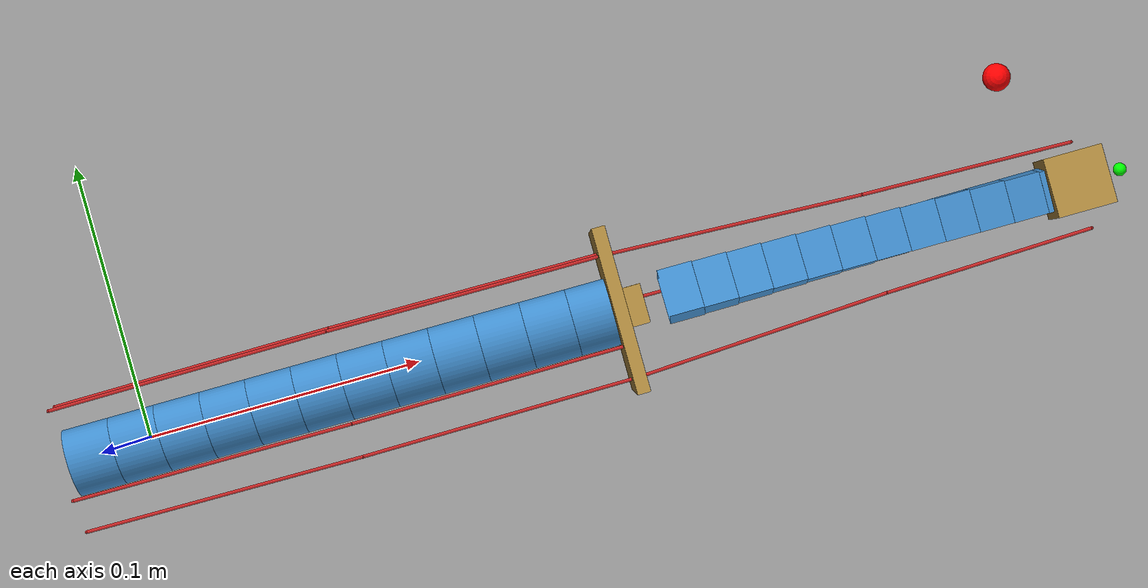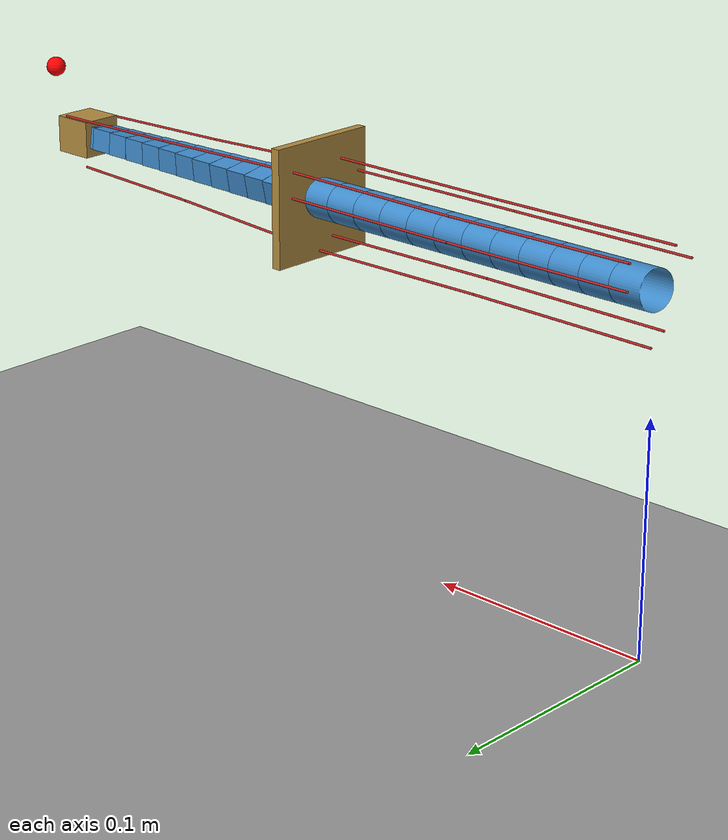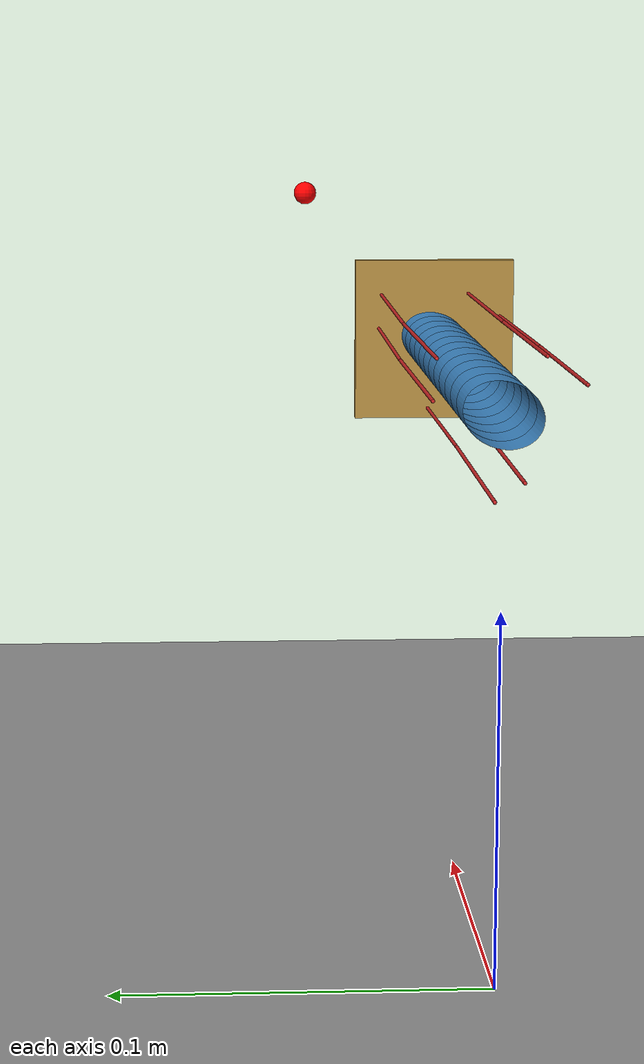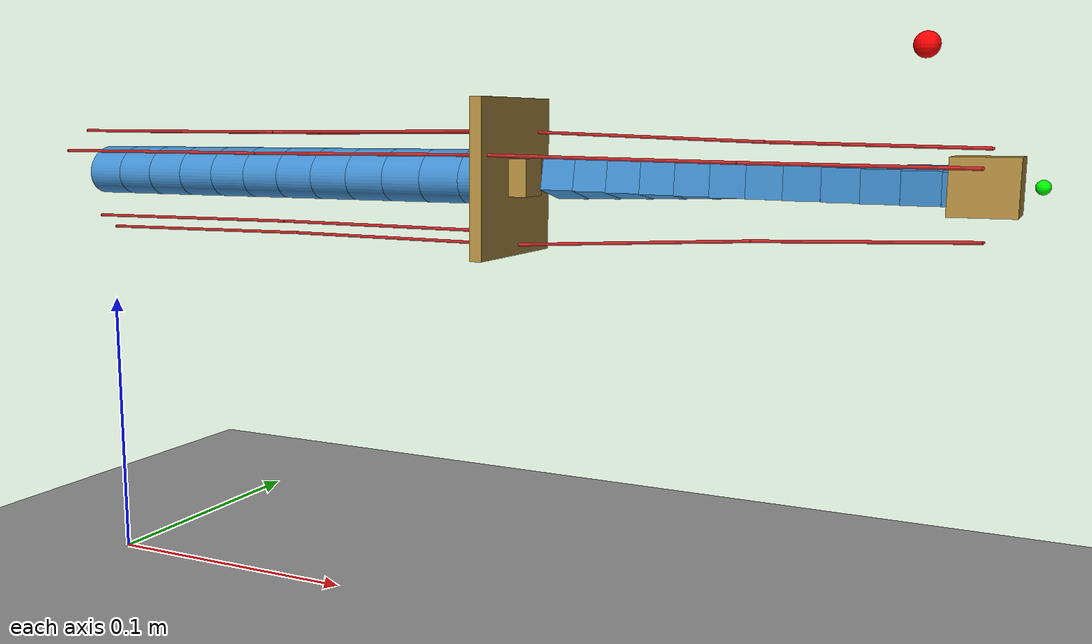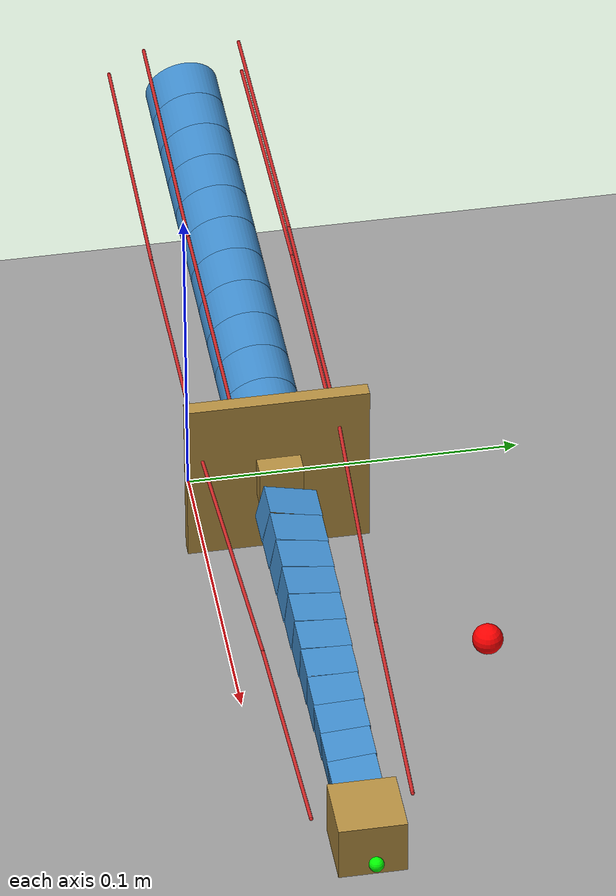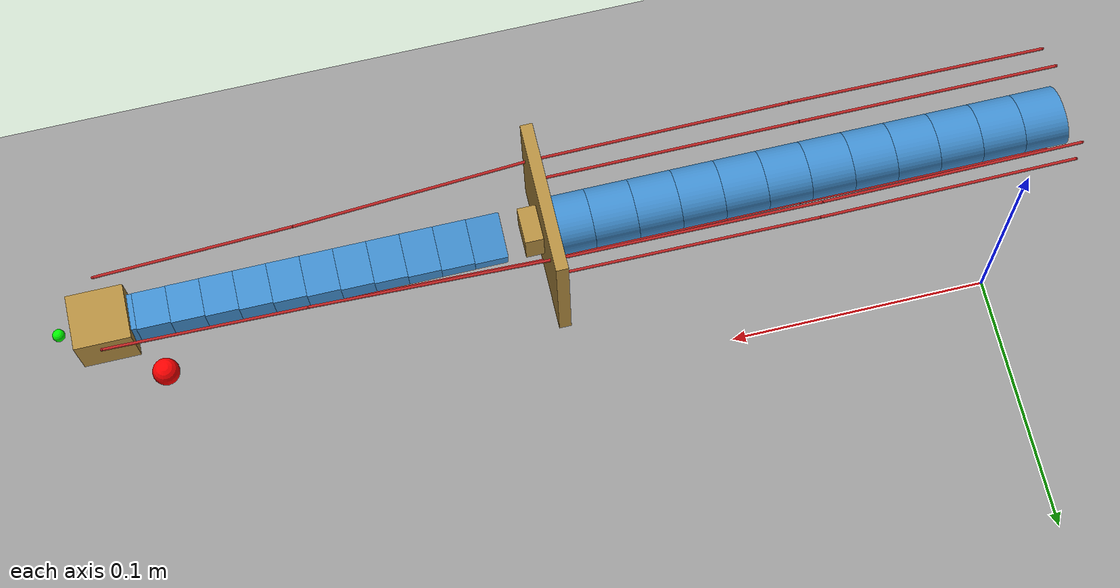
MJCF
<?xml version='1.0' encoding='utf-8'?>
<mujoco model="serial_tendon_family"><compiler angle="radian" autolimits="true" /><option timestep="0.0005" gravity="0 0 -9.8100000000000005" integrator="implicitfast" /><default><joint limited="false" /><geom contype="1" conaffinity="2" friction="0 0 0" /></default><asset><mesh name="near_cell_0_section" vertex="0 -0.010500000000000001 -2.3472756961658466e-18 0 -0.010410171044425008 -0.0010964200146484364 0 -0.010142221176035218 -0.0021740799788611772 0 -0.0097007350913685102 -0.003214540831866757 0 -0.0090932667397366045 -0.0042000000000000023 0 -0.0083302100730579687 -0.0051135960036732542 0 -0.0074246212024587479 -0.0059396969619670012 0 -0.0063919950045915651 -0.0066641680584463778 0 -0.0052499999999999995 -0.0072746133917892851 0 -0.0040181760398334421 -0.0077605880730948103 0 -0.0027175999735764679 -0.0081137769408281737 0 -0.0013705250183105408 -0.0083281368355400086 0 1.1255721090592927e-18 -0.0084000000000000012 0 0.0013705250183105419 -0.0083281368355400086 0 0.0027175999735764688 -0.0081137769408281737 0 0.0040181760398334421 -0.0077605880730948085 0 0.0052499999999999986 -0.0072746133917892843 0 0.0063919950045915643 -0.006664168058446376 0 0.0074246212024587505 -0.0059396969619669986 0 0.0083302100730579705 -0.0051135960036732542 0 0.0090932667397366045 -0.0042000000000000006 0 0.009700735091368512 -0.0032145408318667535 0 0.010142221176035218 -0.0021740799788611742 0 0.010410171044425008 -0.001096420014648434 0 0.010500000000000001 1.5324997473316624e-18 0 0.010410171044425012 0.0010964200146484334 0 0.010142221176035219 0.0021740799788611737 0 0.009700735091368512 0.0032145408318667518 0 0.0090932667397366062 0.0042000000000000006 0 0.0083302100730579705 0.0051135960036732542 0 0.0074246212024587513 0.0059396969619669978 0 0.0063919950045915669 0.0066641680584463752 0 0.0052500000000000029 0.007274613391789286 0 0.0040181760398334473 0.0077605880730948085 0 0.002717599973576474 0.0081137769408281737 0 0.0013705250183105491 0.0083281368355400068 0 -2.5821037107088908e-19 0.0084000000000000012 0 -0.0013705250183105411 0.0083281368355400086 0 -0.0027175999735764649 0.0081137769408281737 0 -0.0040181760398334387 0.0077605880730948111 0 -0.0052499999999999951 0.0072746133917892869 0 -0.0063919950045915608 0.0066641680584463786 0 -0.0074246212024587479 0.0059396969619669986 0 -0.0083302100730579687 0.0051135960036732542 0 -0.0090932667397366027 0.0042000000000000015 0 -0.0097007350913685085 0.003214540831866757 0 -0.010142221176035216 0.0021740799788611794 0 -0.010410171044425006 0.0010964200146484388 0.014166666666666668 -0.010500000000000001 -2.3472756961658466e-18 0.014166666666666668 -0.010410171044425008 -0.0010964200146484364 0.014166666666666668 -0.010142221176035218 -0.0021740799788611772 0.014166666666666668 -0.0097007350913685102 -0.003214540831866757 0.014166666666666668 -0.0090932667397366045 -0.0042000000000000023 0.014166666666666668 -0.0083302100730579687 -0.0051135960036732542 0.014166666666666668 -0.0074246212024587479 -0.0059396969619670012 0.014166666666666668 -0.0063919950045915651 -0.0066641680584463778 0.014166666666666668 -0.0052499999999999995 -0.0072746133917892851 0.014166666666666668 -0.0040181760398334421 -0.0077605880730948103 0.014166666666666668 -0.0027175999735764679 -0.0081137769408281737 0.014166666666666668 -0.0013705250183105408 -0.0083281368355400086 0.014166666666666668 1.1255721090592927e-18 -0.0084000000000000012 0.014166666666666668 0.0013705250183105419 -0.0083281368355400086 0.014166666666666668 0.0027175999735764688 -0.0081137769408281737 0.014166666666666668 0.0040181760398334421 -0.0077605880730948085 0.014166666666666668 0.0052499999999999986 -0.0072746133917892843 0.014166666666666668 0.0063919950045915643 -0.006664168058446376 0.014166666666666668 0.0074246212024587505 -0.0059396969619669986 0.014166666666666668 0.0083302100730579705 -0.0051135960036732542 0.014166666666666668 0.0090932667397366045 -0.0042000000000000006 0.014166666666666668 0.009700735091368512 -0.0032145408318667535 0.014166666666666668 0.010142221176035218 -0.0021740799788611742 0.014166666666666668 0.010410171044425008 -0.001096420014648434 0.014166666666666668 0.010500000000000001 1.5324997473316624e-18 0.014166666666666668 0.010410171044425012 0.0010964200146484334 0.014166666666666668 0.010142221176035219 0.0021740799788611737 0.014166666666666668 0.009700735091368512 0.0032145408318667518 0.014166666666666668 0.0090932667397366062 0.0042000000000000006 0.014166666666666668 0.0083302100730579705 0.0051135960036732542 0.014166666666666668 0.0074246212024587513 0.0059396969619669978 0.014166666666666668 0.0063919950045915669 0.0066641680584463752 0.014166666666666668 0.0052500000000000029 0.007274613391789286 0.014166666666666668 0.0040181760398334473 0.0077605880730948085 0.014166666666666668 0.002717599973576474 0.0081137769408281737 0.014166666666666668 0.0013705250183105491 0.0083281368355400068 0.014166666666666668 -2.5821037107088908e-19 0.0084000000000000012 0.014166666666666668 -0.0013705250183105411 0.0083281368355400086 0.014166666666666668 -0.0027175999735764649 0.0081137769408281737 0.014166666666666668 -0.0040181760398334387 0.0077605880730948111 0.014166666666666668 -0.0052499999999999951 0.0072746133917892869 0.014166666666666668 -0.0063919950045915608 0.0066641680584463786 0.014166666666666668 -0.0074246212024587479 0.0059396969619669986 0.014166666666666668 -0.0083302100730579687 0.0051135960036732542 0.014166666666666668 -0.0090932667397366027 0.0042000000000000015 0.014166666666666668 -0.0097007350913685085 0.003214540831866757 0.014166666666666668 -0.010142221176035216 0.0021740799788611794 0.014166666666666668 -0.010410171044425006 0.0010964200146484388" face="0 1 49 0 49 48 1 2 50 1 50 49 2 3 51 2 51 50 3 4 52 3 52 51 4 5 53 4 53 52 5 6 54 5 54 53 6 7 55 6 55 54 7 8 56 7 56 55 8 9 57 8 57 56 9 10 58 9 58 57 10 11 59 10 59 58 11 12 60 11 60 59 12 13 61 12 61 60 13 14 62 13 62 61 14 15 63 14 63 62 15 16 64 15 64 63 16 17 65 16 65 64 17 18 66 17 66 65 18 19 67 18 67 66 19 20 68 19 68 67 20 21 69 20 69 68 21 22 70 21 70 69 22 23 71 22 71 70 23 24 72 23 72 71 24 25 73 24 73 72 25 26 74 25 74 73 26 27 75 26 75 74 27 28 76 27 76 75 28 29 77 28 77 76 29 30 78 29 78 77 30 31 79 30 79 78 31 32 80 31 80 79 32 33 81 32 81 80 33 34 82 33 82 81 34 35 83 34 83 82 35 36 84 35 84 83 36 37 85 36 85 84 37 38 86 37 86 85 38 39 87 38 87 86 39 40 88 39 88 87 40 41 89 40 89 88 41 42 90 41 90 89 42 43 91 42 91 90 43 44 92 43 92 91 44 45 93 44 93 92 45 46 94 45 94 93 46 47 95 46 95 94 47 0 48 47 48 95" /><mesh name="near_cell_1_section" vertex="0 -0.010500000000000001 -2.3472756961658466e-18 0 -0.010410171044425008 -0.0010964200146484364 0 -0.010142221176035218 -0.0021740799788611772 0 -0.0097007350913685102 -0.003214540831866757 0 -0.0090932667397366045 -0.0042000000000000023 0 -0.0083302100730579687 -0.0051135960036732542 0 -0.0074246212024587479 -0.0059396969619670012 0 -0.0063919950045915651 -0.0066641680584463778 0 -0.0052499999999999995 -0.0072746133917892851 0 -0.0040181760398334421 -0.0077605880730948103 0 -0.0027175999735764679 -0.0081137769408281737 0 -0.0013705250183105408 -0.0083281368355400086 0 1.1255721090592927e-18 -0.0084000000000000012 0 0.0013705250183105419 -0.0083281368355400086 0 0.0027175999735764688 -0.0081137769408281737 0 0.0040181760398334421 -0.0077605880730948085 0 0.0052499999999999986 -0.0072746133917892843 0 0.0063919950045915643 -0.006664168058446376 0 0.0074246212024587505 -0.0059396969619669986 0 0.0083302100730579705 -0.0051135960036732542 0 0.0090932667397366045 -0.0042000000000000006 0 0.009700735091368512 -0.0032145408318667535 0 0.010142221176035218 -0.0021740799788611742 0 0.010410171044425008 -0.001096420014648434 0 0.010500000000000001 1.5324997473316624e-18 0 0.010410171044425012 0.0010964200146484334 0 0.010142221176035219 0.0021740799788611737 0 0.009700735091368512 0.0032145408318667518 0 0.0090932667397366062 0.0042000000000000006 0 0.0083302100730579705 0.0051135960036732542 0 0.0074246212024587513 0.0059396969619669978 0 0.0063919950045915669 0.0066641680584463752 0 0.0052500000000000029 0.007274613391789286 0 0.0040181760398334473 0.0077605880730948085 0 0.002717599973576474 0.0081137769408281737 0 0.0013705250183105491 0.0083281368355400068 0 -2.5821037107088908e-19 0.0084000000000000012 0 -0.0013705250183105411 0.0083281368355400086 0 -0.0027175999735764649 0.0081137769408281737 0 -0.0040181760398334387 0.0077605880730948111 0 -0.0052499999999999951 0.0072746133917892869 0 -0.0063919950045915608 0.0066641680584463786 0 -0.0074246212024587479 0.0059396969619669986 0 -0.0083302100730579687 0.0051135960036732542 0 -0.0090932667397366027 0.0042000000000000015 0 -0.0097007350913685085 0.003214540831866757 0 -0.010142221176035216 0.0021740799788611794 0 -0.010410171044425006 0.0010964200146484388 0.014166666666666668 -0.010500000000000001 -2.3472756961658466e-18 0.014166666666666668 -0.010410171044425008 -0.0010964200146484364 0.014166666666666668 -0.010142221176035218 -0.0021740799788611772 0.014166666666666668 -0.0097007350913685102 -0.003214540831866757 0.014166666666666668 -0.0090932667397366045 -0.0042000000000000023 0.014166666666666668 -0.0083302100730579687 -0.0051135960036732542 0.014166666666666668 -0.0074246212024587479 -0.0059396969619670012 0.014166666666666668 -0.0063919950045915651 -0.0066641680584463778 0.014166666666666668 -0.0052499999999999995 -0.0072746133917892851 0.014166666666666668 -0.0040181760398334421 -0.0077605880730948103 0.014166666666666668 -0.0027175999735764679 -0.0081137769408281737 0.014166666666666668 -0.0013705250183105408 -0.0083281368355400086 0.014166666666666668 1.1255721090592927e-18 -0.0084000000000000012 0.014166666666666668 0.0013705250183105419 -0.0083281368355400086 0.014166666666666668 0.0027175999735764688 -0.0081137769408281737 0.014166666666666668 0.0040181760398334421 -0.0077605880730948085 0.014166666666666668 0.0052499999999999986 -0.0072746133917892843 0.014166666666666668 0.0063919950045915643 -0.006664168058446376 0.014166666666666668 0.0074246212024587505 -0.0059396969619669986 0.014166666666666668 0.0083302100730579705 -0.0051135960036732542 0.014166666666666668 0.0090932667397366045 -0.0042000000000000006 0.014166666666666668 0.009700735091368512 -0.0032145408318667535 0.014166666666666668 0.010142221176035218 -0.0021740799788611742 0.014166666666666668 0.010410171044425008 -0.001096420014648434 0.014166666666666668 0.010500000000000001 1.5324997473316624e-18 0.014166666666666668 0.010410171044425012 0.0010964200146484334 0.014166666666666668 0.010142221176035219 0.0021740799788611737 0.014166666666666668 0.009700735091368512 0.0032145408318667518 0.014166666666666668 0.0090932667397366062 0.0042000000000000006 0.014166666666666668 0.0083302100730579705 0.0051135960036732542 0.014166666666666668 0.0074246212024587513 0.0059396969619669978 0.014166666666666668 0.0063919950045915669 0.0066641680584463752 0.014166666666666668 0.0052500000000000029 0.007274613391789286 0.014166666666666668 0.0040181760398334473 0.0077605880730948085 0.014166666666666668 0.002717599973576474 0.0081137769408281737 0.014166666666666668 0.0013705250183105491 0.0083281368355400068 0.014166666666666668 -2.5821037107088908e-19 0.0084000000000000012 0.014166666666666668 -0.0013705250183105411 0.0083281368355400086 0.014166666666666668 -0.0027175999735764649 0.0081137769408281737 0.014166666666666668 -0.0040181760398334387 0.0077605880730948111 0.014166666666666668 -0.0052499999999999951 0.0072746133917892869 0.014166666666666668 -0.0063919950045915608 0.0066641680584463786 0.014166666666666668 -0.0074246212024587479 0.0059396969619669986 0.014166666666666668 -0.0083302100730579687 0.0051135960036732542 0.014166666666666668 -0.0090932667397366027 0.0042000000000000015 0.014166666666666668 -0.0097007350913685085 0.003214540831866757 0.014166666666666668 -0.010142221176035216 0.0021740799788611794 0.014166666666666668 -0.010410171044425006 0.0010964200146484388" face="0 1 49 0 49 48 1 2 50 1 50 49 2 3 51 2 51 50 3 4 52 3 52 51 4 5 53 4 53 52 5 6 54 5 54 53 6 7 55 6 55 54 7 8 56 7 56 55 8 9 57 8 57 56 9 10 58 9 58 57 10 11 59 10 59 58 11 12 60 11 60 59 12 13 61 12 61 60 13 14 62 13 62 61 14 15 63 14 63 62 15 16 64 15 64 63 16 17 65 16 65 64 17 18 66 17 66 65 18 19 67 18 67 66 19 20 68 19 68 67 20 21 69 20 69 68 21 22 70 21 70 69 22 23 71 22 71 70 23 24 72 23 72 71 24 25 73 24 73 72 25 26 74 25 74 73 26 27 75 26 75 74 27 28 76 27 76 75 28 29 77 28 77 76 29 30 78 29 78 77 30 31 79 30 79 78 31 32 80 31 80 79 32 33 81 32 81 80 33 34 82 33 82 81 34 35 83 34 83 82 35 36 84 35 84 83 36 37 85 36 85 84 37 38 86 37 86 85 38 39 87 38 87 86 39 40 88 39 88 87 40 41 89 40 89 88 41 42 90 41 90 89 42 43 91 42 91 90 43 44 92 43 92 91 44 45 93 44 93 92 45 46 94 45 94 93 46 47 95 46 95 94 47 0 48 47 48 95" /><mesh name="near_cell_2_section" vertex="0 -0.010500000000000001 -2.3472756961658466e-18 0 -0.010410171044425008 -0.0010964200146484364 0 -0.010142221176035218 -0.0021740799788611772 0 -0.0097007350913685102 -0.003214540831866757 0 -0.0090932667397366045 -0.0042000000000000023 0 -0.0083302100730579687 -0.0051135960036732542 0 -0.0074246212024587479 -0.0059396969619670012 0 -0.0063919950045915651 -0.0066641680584463778 0 -0.0052499999999999995 -0.0072746133917892851 0 -0.0040181760398334421 -0.0077605880730948103 0 -0.0027175999735764679 -0.0081137769408281737 0 -0.0013705250183105408 -0.0083281368355400086 0 1.1255721090592927e-18 -0.0084000000000000012 0 0.0013705250183105419 -0.0083281368355400086 0 0.0027175999735764688 -0.0081137769408281737 0 0.0040181760398334421 -0.0077605880730948085 0 0.0052499999999999986 -0.0072746133917892843 0 0.0063919950045915643 -0.006664168058446376 0 0.0074246212024587505 -0.0059396969619669986 0 0.0083302100730579705 -0.0051135960036732542 0 0.0090932667397366045 -0.0042000000000000006 0 0.009700735091368512 -0.0032145408318667535 0 0.010142221176035218 -0.0021740799788611742 0 0.010410171044425008 -0.001096420014648434 0 0.010500000000000001 1.5324997473316624e-18 0 0.010410171044425012 0.0010964200146484334 0 0.010142221176035219 0.0021740799788611737 0 0.009700735091368512 0.0032145408318667518 0 0.0090932667397366062 0.0042000000000000006 0 0.0083302100730579705 0.0051135960036732542 0 0.0074246212024587513 0.0059396969619669978 0 0.0063919950045915669 0.0066641680584463752 0 0.0052500000000000029 0.007274613391789286 0 0.0040181760398334473 0.0077605880730948085 0 0.002717599973576474 0.0081137769408281737 0 0.0013705250183105491 0.0083281368355400068 0 -2.5821037107088908e-19 0.0084000000000000012 0 -0.0013705250183105411 0.0083281368355400086 0 -0.0027175999735764649 0.0081137769408281737 0 -0.0040181760398334387 0.0077605880730948111 0 -0.0052499999999999951 0.0072746133917892869 0 -0.0063919950045915608 0.0066641680584463786 0 -0.0074246212024587479 0.0059396969619669986 0 -0.0083302100730579687 0.0051135960036732542 0 -0.0090932667397366027 0.0042000000000000015 0 -0.0097007350913685085 0.003214540831866757 0 -0.010142221176035216 0.0021740799788611794 0 -0.010410171044425006 0.0010964200146484388 0.014166666666666668 -0.010500000000000001 -2.3472756961658466e-18 0.014166666666666668 -0.010410171044425008 -0.0010964200146484364 0.014166666666666668 -0.010142221176035218 -0.0021740799788611772 0.014166666666666668 -0.0097007350913685102 -0.003214540831866757 0.014166666666666668 -0.0090932667397366045 -0.0042000000000000023 0.014166666666666668 -0.0083302100730579687 -0.0051135960036732542 0.014166666666666668 -0.0074246212024587479 -0.0059396969619670012 0.014166666666666668 -0.0063919950045915651 -0.0066641680584463778 0.014166666666666668 -0.0052499999999999995 -0.0072746133917892851 0.014166666666666668 -0.0040181760398334421 -0.0077605880730948103 0.014166666666666668 -0.0027175999735764679 -0.0081137769408281737 0.014166666666666668 -0.0013705250183105408 -0.0083281368355400086 0.014166666666666668 1.1255721090592927e-18 -0.0084000000000000012 0.014166666666666668 0.0013705250183105419 -0.0083281368355400086 0.014166666666666668 0.0027175999735764688 -0.0081137769408281737 0.014166666666666668 0.0040181760398334421 -0.0077605880730948085 0.014166666666666668 0.0052499999999999986 -0.0072746133917892843 0.014166666666666668 0.0063919950045915643 -0.006664168058446376 0.014166666666666668 0.0074246212024587505 -0.0059396969619669986 0.014166666666666668 0.0083302100730579705 -0.0051135960036732542 0.014166666666666668 0.0090932667397366045 -0.0042000000000000006 0.014166666666666668 0.009700735091368512 -0.0032145408318667535 0.014166666666666668 0.010142221176035218 -0.0021740799788611742 0.014166666666666668 0.010410171044425008 -0.001096420014648434 0.014166666666666668 0.010500000000000001 1.5324997473316624e-18 0.014166666666666668 0.010410171044425012 0.0010964200146484334 0.014166666666666668 0.010142221176035219 0.0021740799788611737 0.014166666666666668 0.009700735091368512 0.0032145408318667518 0.014166666666666668 0.0090932667397366062 0.0042000000000000006 0.014166666666666668 0.0083302100730579705 0.0051135960036732542 0.014166666666666668 0.0074246212024587513 0.0059396969619669978 0.014166666666666668 0.0063919950045915669 0.0066641680584463752 0.014166666666666668 0.0052500000000000029 0.007274613391789286 0.014166666666666668 0.0040181760398334473 0.0077605880730948085 0.014166666666666668 0.002717599973576474 0.0081137769408281737 0.014166666666666668 0.0013705250183105491 0.0083281368355400068 0.014166666666666668 -2.5821037107088908e-19 0.0084000000000000012 0.014166666666666668 -0.0013705250183105411 0.0083281368355400086 0.014166666666666668 -0.0027175999735764649 0.0081137769408281737 0.014166666666666668 -0.0040181760398334387 0.0077605880730948111 0.014166666666666668 -0.0052499999999999951 0.0072746133917892869 0.014166666666666668 -0.0063919950045915608 0.0066641680584463786 0.014166666666666668 -0.0074246212024587479 0.0059396969619669986 0.014166666666666668 -0.0083302100730579687 0.0051135960036732542 0.014166666666666668 -0.0090932667397366027 0.0042000000000000015 0.014166666666666668 -0.0097007350913685085 0.003214540831866757 0.014166666666666668 -0.010142221176035216 0.0021740799788611794 0.014166666666666668 -0.010410171044425006 0.0010964200146484388" face="0 1 49 0 49 48 1 2 50 1 50 49 2 3 51 2 51 50 3 4 52 3 52 51 4 5 53 4 53 52 5 6 54 5 54 53 6 7 55 6 55 54 7 8 56 7 56 55 8 9 57 8 57 56 9 10 58 9 58 57 10 11 59 10 59 58 11 12 60 11 60 59 12 13 61 12 61 60 13 14 62 13 62 61 14 15 63 14 63 62 15 16 64 15 64 63 16 17 65 16 65 64 17 18 66 17 66 65 18 19 67 18 67 66 19 20 68 19 68 67 20 21 69 20 69 68 21 22 70 21 70 69 22 23 71 22 71 70 23 24 72 23 72 71 24 25 73 24 73 72 25 26 74 25 74 73 26 27 75 26 75 74 27 28 76 27 76 75 28 29 77 28 77 76 29 30 78 29 78 77 30 31 79 30 79 78 31 32 80 31 80 79 32 33 81 32 81 80 33 34 82 33 82 81 34 35 83 34 83 82 35 36 84 35 84 83 36 37 85 36 85 84 37 38 86 37 86 85 38 39 87 38 87 86 39 40 88 39 88 87 40 41 89 40 89 88 41 42 90 41 90 89 42 43 91 42 91 90 43 44 92 43 92 91 44 45 93 44 93 92 45 46 94 45 94 93 46 47 95 46 95 94 47 0 48 47 48 95" /><mesh name="near_cell_3_section" vertex="0 -0.010500000000000001 -2.3472756961658466e-18 0 -0.010410171044425008 -0.0010964200146484364 0 -0.010142221176035218 -0.0021740799788611772 0 -0.0097007350913685102 -0.003214540831866757 0 -0.0090932667397366045 -0.0042000000000000023 0 -0.0083302100730579687 -0.0051135960036732542 0 -0.0074246212024587479 -0.0059396969619670012 0 -0.0063919950045915651 -0.0066641680584463778 0 -0.0052499999999999995 -0.0072746133917892851 0 -0.0040181760398334421 -0.0077605880730948103 0 -0.0027175999735764679 -0.0081137769408281737 0 -0.0013705250183105408 -0.0083281368355400086 0 1.1255721090592927e-18 -0.0084000000000000012 0 0.0013705250183105419 -0.0083281368355400086 0 0.0027175999735764688 -0.0081137769408281737 0 0.0040181760398334421 -0.0077605880730948085 0 0.0052499999999999986 -0.0072746133917892843 0 0.0063919950045915643 -0.006664168058446376 0 0.0074246212024587505 -0.0059396969619669986 0 0.0083302100730579705 -0.0051135960036732542 0 0.0090932667397366045 -0.0042000000000000006 0 0.009700735091368512 -0.0032145408318667535 0 0.010142221176035218 -0.0021740799788611742 0 0.010410171044425008 -0.001096420014648434 0 0.010500000000000001 1.5324997473316624e-18 0 0.010410171044425012 0.0010964200146484334 0 0.010142221176035219 0.0021740799788611737 0 0.009700735091368512 0.0032145408318667518 0 0.0090932667397366062 0.0042000000000000006 0 0.0083302100730579705 0.0051135960036732542 0 0.0074246212024587513 0.0059396969619669978 0 0.0063919950045915669 0.0066641680584463752 0 0.0052500000000000029 0.007274613391789286 0 0.0040181760398334473 0.0077605880730948085 0 0.002717599973576474 0.0081137769408281737 0 0.0013705250183105491 0.0083281368355400068 0 -2.5821037107088908e-19 0.0084000000000000012 0 -0.0013705250183105411 0.0083281368355400086 0 -0.0027175999735764649 0.0081137769408281737 0 -0.0040181760398334387 0.0077605880730948111 0 -0.0052499999999999951 0.0072746133917892869 0 -0.0063919950045915608 0.0066641680584463786 0 -0.0074246212024587479 0.0059396969619669986 0 -0.0083302100730579687 0.0051135960036732542 0 -0.0090932667397366027 0.0042000000000000015 0 -0.0097007350913685085 0.003214540831866757 0 -0.010142221176035216 0.0021740799788611794 0 -0.010410171044425006 0.0010964200146484388 0.014166666666666668 -0.010500000000000001 -2.3472756961658466e-18 0.014166666666666668 -0.010410171044425008 -0.0010964200146484364 0.014166666666666668 -0.010142221176035218 -0.0021740799788611772 0.014166666666666668 -0.0097007350913685102 -0.003214540831866757 0.014166666666666668 -0.0090932667397366045 -0.0042000000000000023 0.014166666666666668 -0.0083302100730579687 -0.0051135960036732542 0.014166666666666668 -0.0074246212024587479 -0.0059396969619670012 0.014166666666666668 -0.0063919950045915651 -0.0066641680584463778 0.014166666666666668 -0.0052499999999999995 -0.0072746133917892851 0.014166666666666668 -0.0040181760398334421 -0.0077605880730948103 0.014166666666666668 -0.0027175999735764679 -0.0081137769408281737 0.014166666666666668 -0.0013705250183105408 -0.0083281368355400086 0.014166666666666668 1.1255721090592927e-18 -0.0084000000000000012 0.014166666666666668 0.0013705250183105419 -0.0083281368355400086 0.014166666666666668 0.0027175999735764688 -0.0081137769408281737 0.014166666666666668 0.0040181760398334421 -0.0077605880730948085 0.014166666666666668 0.0052499999999999986 -0.0072746133917892843 0.014166666666666668 0.0063919950045915643 -0.006664168058446376 0.014166666666666668 0.0074246212024587505 -0.0059396969619669986 0.014166666666666668 0.0083302100730579705 -0.0051135960036732542 0.014166666666666668 0.0090932667397366045 -0.0042000000000000006 0.014166666666666668 0.009700735091368512 -0.0032145408318667535 0.014166666666666668 0.010142221176035218 -0.0021740799788611742 0.014166666666666668 0.010410171044425008 -0.001096420014648434 0.014166666666666668 0.010500000000000001 1.5324997473316624e-18 0.014166666666666668 0.010410171044425012 0.0010964200146484334 0.014166666666666668 0.010142221176035219 0.0021740799788611737 0.014166666666666668 0.009700735091368512 0.0032145408318667518 0.014166666666666668 0.0090932667397366062 0.0042000000000000006 0.014166666666666668 0.0083302100730579705 0.0051135960036732542 0.014166666666666668 0.0074246212024587513 0.0059396969619669978 0.014166666666666668 0.0063919950045915669 0.0066641680584463752 0.014166666666666668 0.0052500000000000029 0.007274613391789286 0.014166666666666668 0.0040181760398334473 0.0077605880730948085 0.014166666666666668 0.002717599973576474 0.0081137769408281737 0.014166666666666668 0.0013705250183105491 0.0083281368355400068 0.014166666666666668 -2.5821037107088908e-19 0.0084000000000000012 0.014166666666666668 -0.0013705250183105411 0.0083281368355400086 0.014166666666666668 -0.0027175999735764649 0.0081137769408281737 0.014166666666666668 -0.0040181760398334387 0.0077605880730948111 0.014166666666666668 -0.0052499999999999951 0.0072746133917892869 0.014166666666666668 -0.0063919950045915608 0.0066641680584463786 0.014166666666666668 -0.0074246212024587479 0.0059396969619669986 0.014166666666666668 -0.0083302100730579687 0.0051135960036732542 0.014166666666666668 -0.0090932667397366027 0.0042000000000000015 0.014166666666666668 -0.0097007350913685085 0.003214540831866757 0.014166666666666668 -0.010142221176035216 0.0021740799788611794 0.014166666666666668 -0.010410171044425006 0.0010964200146484388" face="0 1 49 0 49 48 1 2 50 1 50 49 2 3 51 2 51 50 3 4 52 3 52 51 4 5 53 4 53 52 5 6 54 5 54 53 6 7 55 6 55 54 7 8 56 7 56 55 8 9 57 8 57 56 9 10 58 9 58 57 10 11 59 10 59 58 11 12 60 11 60 59 12 13 61 12 61 60 13 14 62 13 62 61 14 15 63 14 63 62 15 16 64 15 64 63 16 17 65 16 65 64 17 18 66 17 66 65 18 19 67 18 67 66 19 20 68 19 68 67 20 21 69 20 69 68 21 22 70 21 70 69 22 23 71 22 71 70 23 24 72 23 72 71 24 25 73 24 73 72 25 26 74 25 74 73 26 27 75 26 75 74 27 28 76 27 76 75 28 29 77 28 77 76 29 30 78 29 78 77 30 31 79 30 79 78 31 32 80 31 80 79 32 33 81 32 81 80 33 34 82 33 82 81 34 35 83 34 83 82 35 36 84 35 84 83 36 37 85 36 85 84 37 38 86 37 86 85 38 39 87 38 87 86 39 40 88 39 88 87 40 41 89 40 89 88 41 42 90 41 90 89 42 43 91 42 91 90 43 44 92 43 92 91 44 45 93 44 93 92 45 46 94 45 94 93 46 47 95 46 95 94 47 0 48 47 48 95" /><mesh name="near_cell_4_section" vertex="0 -0.010500000000000001 -2.3472756961658466e-18 0 -0.010410171044425008 -0.0010964200146484364 0 -0.010142221176035218 -0.0021740799788611772 0 -0.0097007350913685102 -0.003214540831866757 0 -0.0090932667397366045 -0.0042000000000000023 0 -0.0083302100730579687 -0.0051135960036732542 0 -0.0074246212024587479 -0.0059396969619670012 0 -0.0063919950045915651 -0.0066641680584463778 0 -0.0052499999999999995 -0.0072746133917892851 0 -0.0040181760398334421 -0.0077605880730948103 0 -0.0027175999735764679 -0.0081137769408281737 0 -0.0013705250183105408 -0.0083281368355400086 0 1.1255721090592927e-18 -0.0084000000000000012 0 0.0013705250183105419 -0.0083281368355400086 0 0.0027175999735764688 -0.0081137769408281737 0 0.0040181760398334421 -0.0077605880730948085 0 0.0052499999999999986 -0.0072746133917892843 0 0.0063919950045915643 -0.006664168058446376 0 0.0074246212024587505 -0.0059396969619669986 0 0.0083302100730579705 -0.0051135960036732542 0 0.0090932667397366045 -0.0042000000000000006 0 0.009700735091368512 -0.0032145408318667535 0 0.010142221176035218 -0.0021740799788611742 0 0.010410171044425008 -0.001096420014648434 0 0.010500000000000001 1.5324997473316624e-18 0 0.010410171044425012 0.0010964200146484334 0 0.010142221176035219 0.0021740799788611737 0 0.009700735091368512 0.0032145408318667518 0 0.0090932667397366062 0.0042000000000000006 0 0.0083302100730579705 0.0051135960036732542 0 0.0074246212024587513 0.0059396969619669978 0 0.0063919950045915669 0.0066641680584463752 0 0.0052500000000000029 0.007274613391789286 0 0.0040181760398334473 0.0077605880730948085 0 0.002717599973576474 0.0081137769408281737 0 0.0013705250183105491 0.0083281368355400068 0 -2.5821037107088908e-19 0.0084000000000000012 0 -0.0013705250183105411 0.0083281368355400086 0 -0.0027175999735764649 0.0081137769408281737 0 -0.0040181760398334387 0.0077605880730948111 0 -0.0052499999999999951 0.0072746133917892869 0 -0.0063919950045915608 0.0066641680584463786 0 -0.0074246212024587479 0.0059396969619669986 0 -0.0083302100730579687 0.0051135960036732542 0 -0.0090932667397366027 0.0042000000000000015 0 -0.0097007350913685085 0.003214540831866757 0 -0.010142221176035216 0.0021740799788611794 0 -0.010410171044425006 0.0010964200146484388 0.014166666666666668 -0.010500000000000001 -2.3472756961658466e-18 0.014166666666666668 -0.010410171044425008 -0.0010964200146484364 0.014166666666666668 -0.010142221176035218 -0.0021740799788611772 0.014166666666666668 -0.0097007350913685102 -0.003214540831866757 0.014166666666666668 -0.0090932667397366045 -0.0042000000000000023 0.014166666666666668 -0.0083302100730579687 -0.0051135960036732542 0.014166666666666668 -0.0074246212024587479 -0.0059396969619670012 0.014166666666666668 -0.0063919950045915651 -0.0066641680584463778 0.014166666666666668 -0.0052499999999999995 -0.0072746133917892851 0.014166666666666668 -0.0040181760398334421 -0.0077605880730948103 0.014166666666666668 -0.0027175999735764679 -0.0081137769408281737 0.014166666666666668 -0.0013705250183105408 -0.0083281368355400086 0.014166666666666668 1.1255721090592927e-18 -0.0084000000000000012 0.014166666666666668 0.0013705250183105419 -0.0083281368355400086 0.014166666666666668 0.0027175999735764688 -0.0081137769408281737 0.014166666666666668 0.0040181760398334421 -0.0077605880730948085 0.014166666666666668 0.0052499999999999986 -0.0072746133917892843 0.014166666666666668 0.0063919950045915643 -0.006664168058446376 0.014166666666666668 0.0074246212024587505 -0.0059396969619669986 0.014166666666666668 0.0083302100730579705 -0.0051135960036732542 0.014166666666666668 0.0090932667397366045 -0.0042000000000000006 0.014166666666666668 0.009700735091368512 -0.0032145408318667535 0.014166666666666668 0.010142221176035218 -0.0021740799788611742 0.014166666666666668 0.010410171044425008 -0.001096420014648434 0.014166666666666668 0.010500000000000001 1.5324997473316624e-18 0.014166666666666668 0.010410171044425012 0.0010964200146484334 0.014166666666666668 0.010142221176035219 0.0021740799788611737 0.014166666666666668 0.009700735091368512 0.0032145408318667518 0.014166666666666668 0.0090932667397366062 0.0042000000000000006 0.014166666666666668 0.0083302100730579705 0.0051135960036732542 0.014166666666666668 0.0074246212024587513 0.0059396969619669978 0.014166666666666668 0.0063919950045915669 0.0066641680584463752 0.014166666666666668 0.0052500000000000029 0.007274613391789286 0.014166666666666668 0.0040181760398334473 0.0077605880730948085 0.014166666666666668 0.002717599973576474 0.0081137769408281737 0.014166666666666668 0.0013705250183105491 0.0083281368355400068 0.014166666666666668 -2.5821037107088908e-19 0.0084000000000000012 0.014166666666666668 -0.0013705250183105411 0.0083281368355400086 0.014166666666666668 -0.0027175999735764649 0.0081137769408281737 0.014166666666666668 -0.0040181760398334387 0.0077605880730948111 0.014166666666666668 -0.0052499999999999951 0.0072746133917892869 0.014166666666666668 -0.0063919950045915608 0.0066641680584463786 0.014166666666666668 -0.0074246212024587479 0.0059396969619669986 0.014166666666666668 -0.0083302100730579687 0.0051135960036732542 0.014166666666666668 -0.0090932667397366027 0.0042000000000000015 0.014166666666666668 -0.0097007350913685085 0.003214540831866757 0.014166666666666668 -0.010142221176035216 0.0021740799788611794 0.014166666666666668 -0.010410171044425006 0.0010964200146484388" face="0 1 49 0 49 48 1 2 50 1 50 49 2 3 51 2 51 50 3 4 52 3 52 51 4 5 53 4 53 52 5 6 54 5 54 53 6 7 55 6 55 54 7 8 56 7 56 55 8 9 57 8 57 56 9 10 58 9 58 57 10 11 59 10 59 58 11 12 60 11 60 59 12 13 61 12 61 60 13 14 62 13 62 61 14 15 63 14 63 62 15 16 64 15 64 63 16 17 65 16 65 64 17 18 66 17 66 65 18 19 67 18 67 66 19 20 68 19 68 67 20 21 69 20 69 68 21 22 70 21 70 69 22 23 71 22 71 70 23 24 72 23 72 71 24 25 73 24 73 72 25 26 74 25 74 73 26 27 75 26 75 74 27 28 76 27 76 75 28 29 77 28 77 76 29 30 78 29 78 77 30 31 79 30 79 78 31 32 80 31 80 79 32 33 81 32 81 80 33 34 82 33 82 81 34 35 83 34 83 82 35 36 84 35 84 83 36 37 85 36 85 84 37 38 86 37 86 85 38 39 87 38 87 86 39 40 88 39 88 87 40 41 89 40 89 88 41 42 90 41 90 89 42 43 91 42 91 90 43 44 92 43 92 91 44 45 93 44 93 92 45 46 94 45 94 93 46 47 95 46 95 94 47 0 48 47 48 95" /><mesh name="near_cell_5_section" vertex="0 -0.010500000000000001 -2.3472756961658466e-18 0 -0.010410171044425008 -0.0010964200146484364 0 -0.010142221176035218 -0.0021740799788611772 0 -0.0097007350913685102 -0.003214540831866757 0 -0.0090932667397366045 -0.0042000000000000023 0 -0.0083302100730579687 -0.0051135960036732542 0 -0.0074246212024587479 -0.0059396969619670012 0 -0.0063919950045915651 -0.0066641680584463778 0 -0.0052499999999999995 -0.0072746133917892851 0 -0.0040181760398334421 -0.0077605880730948103 0 -0.0027175999735764679 -0.0081137769408281737 0 -0.0013705250183105408 -0.0083281368355400086 0 1.1255721090592927e-18 -0.0084000000000000012 0 0.0013705250183105419 -0.0083281368355400086 0 0.0027175999735764688 -0.0081137769408281737 0 0.0040181760398334421 -0.0077605880730948085 0 0.0052499999999999986 -0.0072746133917892843 0 0.0063919950045915643 -0.006664168058446376 0 0.0074246212024587505 -0.0059396969619669986 0 0.0083302100730579705 -0.0051135960036732542 0 0.0090932667397366045 -0.0042000000000000006 0 0.009700735091368512 -0.0032145408318667535 0 0.010142221176035218 -0.0021740799788611742 0 0.010410171044425008 -0.001096420014648434 0 0.010500000000000001 1.5324997473316624e-18 0 0.010410171044425012 0.0010964200146484334 0 0.010142221176035219 0.0021740799788611737 0 0.009700735091368512 0.0032145408318667518 0 0.0090932667397366062 0.0042000000000000006 0 0.0083302100730579705 0.0051135960036732542 0 0.0074246212024587513 0.0059396969619669978 0 0.0063919950045915669 0.0066641680584463752 0 0.0052500000000000029 0.007274613391789286 0 0.0040181760398334473 0.0077605880730948085 0 0.002717599973576474 0.0081137769408281737 0 0.0013705250183105491 0.0083281368355400068 0 -2.5821037107088908e-19 0.0084000000000000012 0 -0.0013705250183105411 0.0083281368355400086 0 -0.0027175999735764649 0.0081137769408281737 0 -0.0040181760398334387 0.0077605880730948111 0 -0.0052499999999999951 0.0072746133917892869 0 -0.0063919950045915608 0.0066641680584463786 0 -0.0074246212024587479 0.0059396969619669986 0 -0.0083302100730579687 0.0051135960036732542 0 -0.0090932667397366027 0.0042000000000000015 0 -0.0097007350913685085 0.003214540831866757 0 -0.010142221176035216 0.0021740799788611794 0 -0.010410171044425006 0.0010964200146484388 0.014166666666666668 -0.010500000000000001 -2.3472756961658466e-18 0.014166666666666668 -0.010410171044425008 -0.0010964200146484364 0.014166666666666668 -0.010142221176035218 -0.0021740799788611772 0.014166666666666668 -0.0097007350913685102 -0.003214540831866757 0.014166666666666668 -0.0090932667397366045 -0.0042000000000000023 0.014166666666666668 -0.0083302100730579687 -0.0051135960036732542 0.014166666666666668 -0.0074246212024587479 -0.0059396969619670012 0.014166666666666668 -0.0063919950045915651 -0.0066641680584463778 0.014166666666666668 -0.0052499999999999995 -0.0072746133917892851 0.014166666666666668 -0.0040181760398334421 -0.0077605880730948103 0.014166666666666668 -0.0027175999735764679 -0.0081137769408281737 0.014166666666666668 -0.0013705250183105408 -0.0083281368355400086 0.014166666666666668 1.1255721090592927e-18 -0.0084000000000000012 0.014166666666666668 0.0013705250183105419 -0.0083281368355400086 0.014166666666666668 0.0027175999735764688 -0.0081137769408281737 0.014166666666666668 0.0040181760398334421 -0.0077605880730948085 0.014166666666666668 0.0052499999999999986 -0.0072746133917892843 0.014166666666666668 0.0063919950045915643 -0.006664168058446376 0.014166666666666668 0.0074246212024587505 -0.0059396969619669986 0.014166666666666668 0.0083302100730579705 -0.0051135960036732542 0.014166666666666668 0.0090932667397366045 -0.0042000000000000006 0.014166666666666668 0.009700735091368512 -0.0032145408318667535 0.014166666666666668 0.010142221176035218 -0.0021740799788611742 0.014166666666666668 0.010410171044425008 -0.001096420014648434 0.014166666666666668 0.010500000000000001 1.5324997473316624e-18 0.014166666666666668 0.010410171044425012 0.0010964200146484334 0.014166666666666668 0.010142221176035219 0.0021740799788611737 0.014166666666666668 0.009700735091368512 0.0032145408318667518 0.014166666666666668 0.0090932667397366062 0.0042000000000000006 0.014166666666666668 0.0083302100730579705 0.0051135960036732542 0.014166666666666668 0.0074246212024587513 0.0059396969619669978 0.014166666666666668 0.0063919950045915669 0.0066641680584463752 0.014166666666666668 0.0052500000000000029 0.007274613391789286 0.014166666666666668 0.0040181760398334473 0.0077605880730948085 0.014166666666666668 0.002717599973576474 0.0081137769408281737 0.014166666666666668 0.0013705250183105491 0.0083281368355400068 0.014166666666666668 -2.5821037107088908e-19 0.0084000000000000012 0.014166666666666668 -0.0013705250183105411 0.0083281368355400086 0.014166666666666668 -0.0027175999735764649 0.0081137769408281737 0.014166666666666668 -0.0040181760398334387 0.0077605880730948111 0.014166666666666668 -0.0052499999999999951 0.0072746133917892869 0.014166666666666668 -0.0063919950045915608 0.0066641680584463786 0.014166666666666668 -0.0074246212024587479 0.0059396969619669986 0.014166666666666668 -0.0083302100730579687 0.0051135960036732542 0.014166666666666668 -0.0090932667397366027 0.0042000000000000015 0.014166666666666668 -0.0097007350913685085 0.003214540831866757 0.014166666666666668 -0.010142221176035216 0.0021740799788611794 0.014166666666666668 -0.010410171044425006 0.0010964200146484388" face="0 1 49 0 49 48 1 2 50 1 50 49 2 3 51 2 51 50 3 4 52 3 52 51 4 5 53 4 53 52 5 6 54 5 54 53 6 7 55 6 55 54 7 8 56 7 56 55 8 9 57 8 57 56 9 10 58 9 58 57 10 11 59 10 59 58 11 12 60 11 60 59 12 13 61 12 61 60 13 14 62 13 62 61 14 15 63 14 63 62 15 16 64 15 64 63 16 17 65 16 65 64 17 18 66 17 66 65 18 19 67 18 67 66 19 20 68 19 68 67 20 21 69 20 69 68 21 22 70 21 70 69 22 23 71 22 71 70 23 24 72 23 72 71 24 25 73 24 73 72 25 26 74 25 74 73 26 27 75 26 75 74 27 28 76 27 76 75 28 29 77 28 77 76 29 30 78 29 78 77 30 31 79 30 79 78 31 32 80 31 80 79 32 33 81 32 81 80 33 34 82 33 82 81 34 35 83 34 83 82 35 36 84 35 84 83 36 37 85 36 85 84 37 38 86 37 86 85 38 39 87 38 87 86 39 40 88 39 88 87 40 41 89 40 89 88 41 42 90 41 90 89 42 43 91 42 91 90 43 44 92 43 92 91 44 45 93 44 93 92 45 46 94 45 94 93 46 47 95 46 95 94 47 0 48 47 48 95" /><mesh name="near_cell_6_section" vertex="0 -0.010500000000000001 -2.3472756961658466e-18 0 -0.010410171044425008 -0.0010964200146484364 0 -0.010142221176035218 -0.0021740799788611772 0 -0.0097007350913685102 -0.003214540831866757 0 -0.0090932667397366045 -0.0042000000000000023 0 -0.0083302100730579687 -0.0051135960036732542 0 -0.0074246212024587479 -0.0059396969619670012 0 -0.0063919950045915651 -0.0066641680584463778 0 -0.0052499999999999995 -0.0072746133917892851 0 -0.0040181760398334421 -0.0077605880730948103 0 -0.0027175999735764679 -0.0081137769408281737 0 -0.0013705250183105408 -0.0083281368355400086 0 1.1255721090592927e-18 -0.0084000000000000012 0 0.0013705250183105419 -0.0083281368355400086 0 0.0027175999735764688 -0.0081137769408281737 0 0.0040181760398334421 -0.0077605880730948085 0 0.0052499999999999986 -0.0072746133917892843 0 0.0063919950045915643 -0.006664168058446376 0 0.0074246212024587505 -0.0059396969619669986 0 0.0083302100730579705 -0.0051135960036732542 0 0.0090932667397366045 -0.0042000000000000006 0 0.009700735091368512 -0.0032145408318667535 0 0.010142221176035218 -0.0021740799788611742 0 0.010410171044425008 -0.001096420014648434 0 0.010500000000000001 1.5324997473316624e-18 0 0.010410171044425012 0.0010964200146484334 0 0.010142221176035219 0.0021740799788611737 0 0.009700735091368512 0.0032145408318667518 0 0.0090932667397366062 0.0042000000000000006 0 0.0083302100730579705 0.0051135960036732542 0 0.0074246212024587513 0.0059396969619669978 0 0.0063919950045915669 0.0066641680584463752 0 0.0052500000000000029 0.007274613391789286 0 0.0040181760398334473 0.0077605880730948085 0 0.002717599973576474 0.0081137769408281737 0 0.0013705250183105491 0.0083281368355400068 0 -2.5821037107088908e-19 0.0084000000000000012 0 -0.0013705250183105411 0.0083281368355400086 0 -0.0027175999735764649 0.0081137769408281737 0 -0.0040181760398334387 0.0077605880730948111 0 -0.0052499999999999951 0.0072746133917892869 0 -0.0063919950045915608 0.0066641680584463786 0 -0.0074246212024587479 0.0059396969619669986 0 -0.0083302100730579687 0.0051135960036732542 0 -0.0090932667397366027 0.0042000000000000015 0 -0.0097007350913685085 0.003214540831866757 0 -0.010142221176035216 0.0021740799788611794 0 -0.010410171044425006 0.0010964200146484388 0.014166666666666668 -0.010500000000000001 -2.3472756961658466e-18 0.014166666666666668 -0.010410171044425008 -0.0010964200146484364 0.014166666666666668 -0.010142221176035218 -0.0021740799788611772 0.014166666666666668 -0.0097007350913685102 -0.003214540831866757 0.014166666666666668 -0.0090932667397366045 -0.0042000000000000023 0.014166666666666668 -0.0083302100730579687 -0.0051135960036732542 0.014166666666666668 -0.0074246212024587479 -0.0059396969619670012 0.014166666666666668 -0.0063919950045915651 -0.0066641680584463778 0.014166666666666668 -0.0052499999999999995 -0.0072746133917892851 0.014166666666666668 -0.0040181760398334421 -0.0077605880730948103 0.014166666666666668 -0.0027175999735764679 -0.0081137769408281737 0.014166666666666668 -0.0013705250183105408 -0.0083281368355400086 0.014166666666666668 1.1255721090592927e-18 -0.0084000000000000012 0.014166666666666668 0.0013705250183105419 -0.0083281368355400086 0.014166666666666668 0.0027175999735764688 -0.0081137769408281737 0.014166666666666668 0.0040181760398334421 -0.0077605880730948085 0.014166666666666668 0.0052499999999999986 -0.0072746133917892843 0.014166666666666668 0.0063919950045915643 -0.006664168058446376 0.014166666666666668 0.0074246212024587505 -0.0059396969619669986 0.014166666666666668 0.0083302100730579705 -0.0051135960036732542 0.014166666666666668 0.0090932667397366045 -0.0042000000000000006 0.014166666666666668 0.009700735091368512 -0.0032145408318667535 0.014166666666666668 0.010142221176035218 -0.0021740799788611742 0.014166666666666668 0.010410171044425008 -0.001096420014648434 0.014166666666666668 0.010500000000000001 1.5324997473316624e-18 0.014166666666666668 0.010410171044425012 0.0010964200146484334 0.014166666666666668 0.010142221176035219 0.0021740799788611737 0.014166666666666668 0.009700735091368512 0.0032145408318667518 0.014166666666666668 0.0090932667397366062 0.0042000000000000006 0.014166666666666668 0.0083302100730579705 0.0051135960036732542 0.014166666666666668 0.0074246212024587513 0.0059396969619669978 0.014166666666666668 0.0063919950045915669 0.0066641680584463752 0.014166666666666668 0.0052500000000000029 0.007274613391789286 0.014166666666666668 0.0040181760398334473 0.0077605880730948085 0.014166666666666668 0.002717599973576474 0.0081137769408281737 0.014166666666666668 0.0013705250183105491 0.0083281368355400068 0.014166666666666668 -2.5821037107088908e-19 0.0084000000000000012 0.014166666666666668 -0.0013705250183105411 0.0083281368355400086 0.014166666666666668 -0.0027175999735764649 0.0081137769408281737 0.014166666666666668 -0.0040181760398334387 0.0077605880730948111 0.014166666666666668 -0.0052499999999999951 0.0072746133917892869 0.014166666666666668 -0.0063919950045915608 0.0066641680584463786 0.014166666666666668 -0.0074246212024587479 0.0059396969619669986 0.014166666666666668 -0.0083302100730579687 0.0051135960036732542 0.014166666666666668 -0.0090932667397366027 0.0042000000000000015 0.014166666666666668 -0.0097007350913685085 0.003214540831866757 0.014166666666666668 -0.010142221176035216 0.0021740799788611794 0.014166666666666668 -0.010410171044425006 0.0010964200146484388" face="0 1 49 0 49 48 1 2 50 1 50 49 2 3 51 2 51 50 3 4 52 3 52 51 4 5 53 4 53 52 5 6 54 5 54 53 6 7 55 6 55 54 7 8 56 7 56 55 8 9 57 8 57 56 9 10 58 9 58 57 10 11 59 10 59 58 11 12 60 11 60 59 12 13 61 12 61 60 13 14 62 13 62 61 14 15 63 14 63 62 15 16 64 15 64 63 16 17 65 16 65 64 17 18 66 17 66 65 18 19 67 18 67 66 19 20 68 19 68 67 20 21 69 20 69 68 21 22 70 21 70 69 22 23 71 22 71 70 23 24 72 23 72 71 24 25 73 24 73 72 25 26 74 25 74 73 26 27 75 26 75 74 27 28 76 27 76 75 28 29 77 28 77 76 29 30 78 29 78 77 30 31 79 30 79 78 31 32 80 31 80 79 32 33 81 32 81 80 33 34 82 33 82 81 34 35 83 34 83 82 35 36 84 35 84 83 36 37 85 36 85 84 37 38 86 37 86 85 38 39 87 38 87 86 39 40 88 39 88 87 40 41 89 40 89 88 41 42 90 41 90 89 42 43 91 42 91 90 43 44 92 43 92 91 44 45 93 44 93 92 45 46 94 45 94 93 46 47 95 46 95 94 47 0 48 47 48 95" /><mesh name="near_cell_7_section" vertex="0 -0.010500000000000001 -2.3472756961658466e-18 0 -0.010410171044425008 -0.0010964200146484364 0 -0.010142221176035218 -0.0021740799788611772 0 -0.0097007350913685102 -0.003214540831866757 0 -0.0090932667397366045 -0.0042000000000000023 0 -0.0083302100730579687 -0.0051135960036732542 0 -0.0074246212024587479 -0.0059396969619670012 0 -0.0063919950045915651 -0.0066641680584463778 0 -0.0052499999999999995 -0.0072746133917892851 0 -0.0040181760398334421 -0.0077605880730948103 0 -0.0027175999735764679 -0.0081137769408281737 0 -0.0013705250183105408 -0.0083281368355400086 0 1.1255721090592927e-18 -0.0084000000000000012 0 0.0013705250183105419 -0.0083281368355400086 0 0.0027175999735764688 -0.0081137769408281737 0 0.0040181760398334421 -0.0077605880730948085 0 0.0052499999999999986 -0.0072746133917892843 0 0.0063919950045915643 -0.006664168058446376 0 0.0074246212024587505 -0.0059396969619669986 0 0.0083302100730579705 -0.0051135960036732542 0 0.0090932667397366045 -0.0042000000000000006 0 0.009700735091368512 -0.0032145408318667535 0 0.010142221176035218 -0.0021740799788611742 0 0.010410171044425008 -0.001096420014648434 0 0.010500000000000001 1.5324997473316624e-18 0 0.010410171044425012 0.0010964200146484334 0 0.010142221176035219 0.0021740799788611737 0 0.009700735091368512 0.0032145408318667518 0 0.0090932667397366062 0.0042000000000000006 0 0.0083302100730579705 0.0051135960036732542 0 0.0074246212024587513 0.0059396969619669978 0 0.0063919950045915669 0.0066641680584463752 0 0.0052500000000000029 0.007274613391789286 0 0.0040181760398334473 0.0077605880730948085 0 0.002717599973576474 0.0081137769408281737 0 0.0013705250183105491 0.0083281368355400068 0 -2.5821037107088908e-19 0.0084000000000000012 0 -0.0013705250183105411 0.0083281368355400086 0 -0.0027175999735764649 0.0081137769408281737 0 -0.0040181760398334387 0.0077605880730948111 0 -0.0052499999999999951 0.0072746133917892869 0 -0.0063919950045915608 0.0066641680584463786 0 -0.0074246212024587479 0.0059396969619669986 0 -0.0083302100730579687 0.0051135960036732542 0 -0.0090932667397366027 0.0042000000000000015 0 -0.0097007350913685085 0.003214540831866757 0 -0.010142221176035216 0.0021740799788611794 0 -0.010410171044425006 0.0010964200146484388 0.014166666666666668 -0.010500000000000001 -2.3472756961658466e-18 0.014166666666666668 -0.010410171044425008 -0.0010964200146484364 0.014166666666666668 -0.010142221176035218 -0.0021740799788611772 0.014166666666666668 -0.0097007350913685102 -0.003214540831866757 0.014166666666666668 -0.0090932667397366045 -0.0042000000000000023 0.014166666666666668 -0.0083302100730579687 -0.0051135960036732542 0.014166666666666668 -0.0074246212024587479 -0.0059396969619670012 0.014166666666666668 -0.0063919950045915651 -0.0066641680584463778 0.014166666666666668 -0.0052499999999999995 -0.0072746133917892851 0.014166666666666668 -0.0040181760398334421 -0.0077605880730948103 0.014166666666666668 -0.0027175999735764679 -0.0081137769408281737 0.014166666666666668 -0.0013705250183105408 -0.0083281368355400086 0.014166666666666668 1.1255721090592927e-18 -0.0084000000000000012 0.014166666666666668 0.0013705250183105419 -0.0083281368355400086 0.014166666666666668 0.0027175999735764688 -0.0081137769408281737 0.014166666666666668 0.0040181760398334421 -0.0077605880730948085 0.014166666666666668 0.0052499999999999986 -0.0072746133917892843 0.014166666666666668 0.0063919950045915643 -0.006664168058446376 0.014166666666666668 0.0074246212024587505 -0.0059396969619669986 0.014166666666666668 0.0083302100730579705 -0.0051135960036732542 0.014166666666666668 0.0090932667397366045 -0.0042000000000000006 0.014166666666666668 0.009700735091368512 -0.0032145408318667535 0.014166666666666668 0.010142221176035218 -0.0021740799788611742 0.014166666666666668 0.010410171044425008 -0.001096420014648434 0.014166666666666668 0.010500000000000001 1.5324997473316624e-18 0.014166666666666668 0.010410171044425012 0.0010964200146484334 0.014166666666666668 0.010142221176035219 0.0021740799788611737 0.014166666666666668 0.009700735091368512 0.0032145408318667518 0.014166666666666668 0.0090932667397366062 0.0042000000000000006 0.014166666666666668 0.0083302100730579705 0.0051135960036732542 0.014166666666666668 0.0074246212024587513 0.0059396969619669978 0.014166666666666668 0.0063919950045915669 0.0066641680584463752 0.014166666666666668 0.0052500000000000029 0.007274613391789286 0.014166666666666668 0.0040181760398334473 0.0077605880730948085 0.014166666666666668 0.002717599973576474 0.0081137769408281737 0.014166666666666668 0.0013705250183105491 0.0083281368355400068 0.014166666666666668 -2.5821037107088908e-19 0.0084000000000000012 0.014166666666666668 -0.0013705250183105411 0.0083281368355400086 0.014166666666666668 -0.0027175999735764649 0.0081137769408281737 0.014166666666666668 -0.0040181760398334387 0.0077605880730948111 0.014166666666666668 -0.0052499999999999951 0.0072746133917892869 0.014166666666666668 -0.0063919950045915608 0.0066641680584463786 0.014166666666666668 -0.0074246212024587479 0.0059396969619669986 0.014166666666666668 -0.0083302100730579687 0.0051135960036732542 0.014166666666666668 -0.0090932667397366027 0.0042000000000000015 0.014166666666666668 -0.0097007350913685085 0.003214540831866757 0.014166666666666668 -0.010142221176035216 0.0021740799788611794 0.014166666666666668 -0.010410171044425006 0.0010964200146484388" face="0 1 49 0 49 48 1 2 50 1 50 49 2 3 51 2 51 50 3 4 52 3 52 51 4 5 53 4 53 52 5 6 54 5 54 53 6 7 55 6 55 54 7 8 56 7 56 55 8 9 57 8 57 56 9 10 58 9 58 57 10 11 59 10 59 58 11 12 60 11 60 59 12 13 61 12 61 60 13 14 62 13 62 61 14 15 63 14 63 62 15 16 64 15 64 63 16 17 65 16 65 64 17 18 66 17 66 65 18 19 67 18 67 66 19 20 68 19 68 67 20 21 69 20 69 68 21 22 70 21 70 69 22 23 71 22 71 70 23 24 72 23 72 71 24 25 73 24 73 72 25 26 74 25 74 73 26 27 75 26 75 74 27 28 76 27 76 75 28 29 77 28 77 76 29 30 78 29 78 77 30 31 79 30 79 78 31 32 80 31 80 79 32 33 81 32 81 80 33 34 82 33 82 81 34 35 83 34 83 82 35 36 84 35 84 83 36 37 85 36 85 84 37 38 86 37 86 85 38 39 87 38 87 86 39 40 88 39 88 87 40 41 89 40 89 88 41 42 90 41 90 89 42 43 91 42 91 90 43 44 92 43 92 91 44 45 93 44 93 92 45 46 94 45 94 93 46 47 95 46 95 94 47 0 48 47 48 95" /><mesh name="near_cell_8_section" vertex="0 -0.010500000000000001 -2.3472756961658466e-18 0 -0.010410171044425008 -0.0010964200146484364 0 -0.010142221176035218 -0.0021740799788611772 0 -0.0097007350913685102 -0.003214540831866757 0 -0.0090932667397366045 -0.0042000000000000023 0 -0.0083302100730579687 -0.0051135960036732542 0 -0.0074246212024587479 -0.0059396969619670012 0 -0.0063919950045915651 -0.0066641680584463778 0 -0.0052499999999999995 -0.0072746133917892851 0 -0.0040181760398334421 -0.0077605880730948103 0 -0.0027175999735764679 -0.0081137769408281737 0 -0.0013705250183105408 -0.0083281368355400086 0 1.1255721090592927e-18 -0.0084000000000000012 0 0.0013705250183105419 -0.0083281368355400086 0 0.0027175999735764688 -0.0081137769408281737 0 0.0040181760398334421 -0.0077605880730948085 0 0.0052499999999999986 -0.0072746133917892843 0 0.0063919950045915643 -0.006664168058446376 0 0.0074246212024587505 -0.0059396969619669986 0 0.0083302100730579705 -0.0051135960036732542 0 0.0090932667397366045 -0.0042000000000000006 0 0.009700735091368512 -0.0032145408318667535 0 0.010142221176035218 -0.0021740799788611742 0 0.010410171044425008 -0.001096420014648434 0 0.010500000000000001 1.5324997473316624e-18 0 0.010410171044425012 0.0010964200146484334 0 0.010142221176035219 0.0021740799788611737 0 0.009700735091368512 0.0032145408318667518 0 0.0090932667397366062 0.0042000000000000006 0 0.0083302100730579705 0.0051135960036732542 0 0.0074246212024587513 0.0059396969619669978 0 0.0063919950045915669 0.0066641680584463752 0 0.0052500000000000029 0.007274613391789286 0 0.0040181760398334473 0.0077605880730948085 0 0.002717599973576474 0.0081137769408281737 0 0.0013705250183105491 0.0083281368355400068 0 -2.5821037107088908e-19 0.0084000000000000012 0 -0.0013705250183105411 0.0083281368355400086 0 -0.0027175999735764649 0.0081137769408281737 0 -0.0040181760398334387 0.0077605880730948111 0 -0.0052499999999999951 0.0072746133917892869 0 -0.0063919950045915608 0.0066641680584463786 0 -0.0074246212024587479 0.0059396969619669986 0 -0.0083302100730579687 0.0051135960036732542 0 -0.0090932667397366027 0.0042000000000000015 0 -0.0097007350913685085 0.003214540831866757 0 -0.010142221176035216 0.0021740799788611794 0 -0.010410171044425006 0.0010964200146484388 0.014166666666666668 -0.010500000000000001 -2.3472756961658466e-18 0.014166666666666668 -0.010410171044425008 -0.0010964200146484364 0.014166666666666668 -0.010142221176035218 -0.0021740799788611772 0.014166666666666668 -0.0097007350913685102 -0.003214540831866757 0.014166666666666668 -0.0090932667397366045 -0.0042000000000000023 0.014166666666666668 -0.0083302100730579687 -0.0051135960036732542 0.014166666666666668 -0.0074246212024587479 -0.0059396969619670012 0.014166666666666668 -0.0063919950045915651 -0.0066641680584463778 0.014166666666666668 -0.0052499999999999995 -0.0072746133917892851 0.014166666666666668 -0.0040181760398334421 -0.0077605880730948103 0.014166666666666668 -0.0027175999735764679 -0.0081137769408281737 0.014166666666666668 -0.0013705250183105408 -0.0083281368355400086 0.014166666666666668 1.1255721090592927e-18 -0.0084000000000000012 0.014166666666666668 0.0013705250183105419 -0.0083281368355400086 0.014166666666666668 0.0027175999735764688 -0.0081137769408281737 0.014166666666666668 0.0040181760398334421 -0.0077605880730948085 0.014166666666666668 0.0052499999999999986 -0.0072746133917892843 0.014166666666666668 0.0063919950045915643 -0.006664168058446376 0.014166666666666668 0.0074246212024587505 -0.0059396969619669986 0.014166666666666668 0.0083302100730579705 -0.0051135960036732542 0.014166666666666668 0.0090932667397366045 -0.0042000000000000006 0.014166666666666668 0.009700735091368512 -0.0032145408318667535 0.014166666666666668 0.010142221176035218 -0.0021740799788611742 0.014166666666666668 0.010410171044425008 -0.001096420014648434 0.014166666666666668 0.010500000000000001 1.5324997473316624e-18 0.014166666666666668 0.010410171044425012 0.0010964200146484334 0.014166666666666668 0.010142221176035219 0.0021740799788611737 0.014166666666666668 0.009700735091368512 0.0032145408318667518 0.014166666666666668 0.0090932667397366062 0.0042000000000000006 0.014166666666666668 0.0083302100730579705 0.0051135960036732542 0.014166666666666668 0.0074246212024587513 0.0059396969619669978 0.014166666666666668 0.0063919950045915669 0.0066641680584463752 0.014166666666666668 0.0052500000000000029 0.007274613391789286 0.014166666666666668 0.0040181760398334473 0.0077605880730948085 0.014166666666666668 0.002717599973576474 0.0081137769408281737 0.014166666666666668 0.0013705250183105491 0.0083281368355400068 0.014166666666666668 -2.5821037107088908e-19 0.0084000000000000012 0.014166666666666668 -0.0013705250183105411 0.0083281368355400086 0.014166666666666668 -0.0027175999735764649 0.0081137769408281737 0.014166666666666668 -0.0040181760398334387 0.0077605880730948111 0.014166666666666668 -0.0052499999999999951 0.0072746133917892869 0.014166666666666668 -0.0063919950045915608 0.0066641680584463786 0.014166666666666668 -0.0074246212024587479 0.0059396969619669986 0.014166666666666668 -0.0083302100730579687 0.0051135960036732542 0.014166666666666668 -0.0090932667397366027 0.0042000000000000015 0.014166666666666668 -0.0097007350913685085 0.003214540831866757 0.014166666666666668 -0.010142221176035216 0.0021740799788611794 0.014166666666666668 -0.010410171044425006 0.0010964200146484388" face="0 1 49 0 49 48 1 2 50 1 50 49 2 3 51 2 51 50 3 4 52 3 52 51 4 5 53 4 53 52 5 6 54 5 54 53 6 7 55 6 55 54 7 8 56 7 56 55 8 9 57 8 57 56 9 10 58 9 58 57 10 11 59 10 59 58 11 12 60 11 60 59 12 13 61 12 61 60 13 14 62 13 62 61 14 15 63 14 63 62 15 16 64 15 64 63 16 17 65 16 65 64 17 18 66 17 66 65 18 19 67 18 67 66 19 20 68 19 68 67 20 21 69 20 69 68 21 22 70 21 70 69 22 23 71 22 71 70 23 24 72 23 72 71 24 25 73 24 73 72 25 26 74 25 74 73 26 27 75 26 75 74 27 28 76 27 76 75 28 29 77 28 77 76 29 30 78 29 78 77 30 31 79 30 79 78 31 32 80 31 80 79 32 33 81 32 81 80 33 34 82 33 82 81 34 35 83 34 83 82 35 36 84 35 84 83 36 37 85 36 85 84 37 38 86 37 86 85 38 39 87 38 87 86 39 40 88 39 88 87 40 41 89 40 89 88 41 42 90 41 90 89 42 43 91 42 91 90 43 44 92 43 92 91 44 45 93 44 93 92 45 46 94 45 94 93 46 47 95 46 95 94 47 0 48 47 48 95" /><mesh name="near_cell_9_section" vertex="0 -0.010500000000000001 -2.3472756961658466e-18 0 -0.010410171044425008 -0.0010964200146484364 0 -0.010142221176035218 -0.0021740799788611772 0 -0.0097007350913685102 -0.003214540831866757 0 -0.0090932667397366045 -0.0042000000000000023 0 -0.0083302100730579687 -0.0051135960036732542 0 -0.0074246212024587479 -0.0059396969619670012 0 -0.0063919950045915651 -0.0066641680584463778 0 -0.0052499999999999995 -0.0072746133917892851 0 -0.0040181760398334421 -0.0077605880730948103 0 -0.0027175999735764679 -0.0081137769408281737 0 -0.0013705250183105408 -0.0083281368355400086 0 1.1255721090592927e-18 -0.0084000000000000012 0 0.0013705250183105419 -0.0083281368355400086 0 0.0027175999735764688 -0.0081137769408281737 0 0.0040181760398334421 -0.0077605880730948085 0 0.0052499999999999986 -0.0072746133917892843 0 0.0063919950045915643 -0.006664168058446376 0 0.0074246212024587505 -0.0059396969619669986 0 0.0083302100730579705 -0.0051135960036732542 0 0.0090932667397366045 -0.0042000000000000006 0 0.009700735091368512 -0.0032145408318667535 0 0.010142221176035218 -0.0021740799788611742 0 0.010410171044425008 -0.001096420014648434 0 0.010500000000000001 1.5324997473316624e-18 0 0.010410171044425012 0.0010964200146484334 0 0.010142221176035219 0.0021740799788611737 0 0.009700735091368512 0.0032145408318667518 0 0.0090932667397366062 0.0042000000000000006 0 0.0083302100730579705 0.0051135960036732542 0 0.0074246212024587513 0.0059396969619669978 0 0.0063919950045915669 0.0066641680584463752 0 0.0052500000000000029 0.007274613391789286 0 0.0040181760398334473 0.0077605880730948085 0 0.002717599973576474 0.0081137769408281737 0 0.0013705250183105491 0.0083281368355400068 0 -2.5821037107088908e-19 0.0084000000000000012 0 -0.0013705250183105411 0.0083281368355400086 0 -0.0027175999735764649 0.0081137769408281737 0 -0.0040181760398334387 0.0077605880730948111 0 -0.0052499999999999951 0.0072746133917892869 0 -0.0063919950045915608 0.0066641680584463786 0 -0.0074246212024587479 0.0059396969619669986 0 -0.0083302100730579687 0.0051135960036732542 0 -0.0090932667397366027 0.0042000000000000015 0 -0.0097007350913685085 0.003214540831866757 0 -0.010142221176035216 0.0021740799788611794 0 -0.010410171044425006 0.0010964200146484388 0.014166666666666668 -0.010500000000000001 -2.3472756961658466e-18 0.014166666666666668 -0.010410171044425008 -0.0010964200146484364 0.014166666666666668 -0.010142221176035218 -0.0021740799788611772 0.014166666666666668 -0.0097007350913685102 -0.003214540831866757 0.014166666666666668 -0.0090932667397366045 -0.0042000000000000023 0.014166666666666668 -0.0083302100730579687 -0.0051135960036732542 0.014166666666666668 -0.0074246212024587479 -0.0059396969619670012 0.014166666666666668 -0.0063919950045915651 -0.0066641680584463778 0.014166666666666668 -0.0052499999999999995 -0.0072746133917892851 0.014166666666666668 -0.0040181760398334421 -0.0077605880730948103 0.014166666666666668 -0.0027175999735764679 -0.0081137769408281737 0.014166666666666668 -0.0013705250183105408 -0.0083281368355400086 0.014166666666666668 1.1255721090592927e-18 -0.0084000000000000012 0.014166666666666668 0.0013705250183105419 -0.0083281368355400086 0.014166666666666668 0.0027175999735764688 -0.0081137769408281737 0.014166666666666668 0.0040181760398334421 -0.0077605880730948085 0.014166666666666668 0.0052499999999999986 -0.0072746133917892843 0.014166666666666668 0.0063919950045915643 -0.006664168058446376 0.014166666666666668 0.0074246212024587505 -0.0059396969619669986 0.014166666666666668 0.0083302100730579705 -0.0051135960036732542 0.014166666666666668 0.0090932667397366045 -0.0042000000000000006 0.014166666666666668 0.009700735091368512 -0.0032145408318667535 0.014166666666666668 0.010142221176035218 -0.0021740799788611742 0.014166666666666668 0.010410171044425008 -0.001096420014648434 0.014166666666666668 0.010500000000000001 1.5324997473316624e-18 0.014166666666666668 0.010410171044425012 0.0010964200146484334 0.014166666666666668 0.010142221176035219 0.0021740799788611737 0.014166666666666668 0.009700735091368512 0.0032145408318667518 0.014166666666666668 0.0090932667397366062 0.0042000000000000006 0.014166666666666668 0.0083302100730579705 0.0051135960036732542 0.014166666666666668 0.0074246212024587513 0.0059396969619669978 0.014166666666666668 0.0063919950045915669 0.0066641680584463752 0.014166666666666668 0.0052500000000000029 0.007274613391789286 0.014166666666666668 0.0040181760398334473 0.0077605880730948085 0.014166666666666668 0.002717599973576474 0.0081137769408281737 0.014166666666666668 0.0013705250183105491 0.0083281368355400068 0.014166666666666668 -2.5821037107088908e-19 0.0084000000000000012 0.014166666666666668 -0.0013705250183105411 0.0083281368355400086 0.014166666666666668 -0.0027175999735764649 0.0081137769408281737 0.014166666666666668 -0.0040181760398334387 0.0077605880730948111 0.014166666666666668 -0.0052499999999999951 0.0072746133917892869 0.014166666666666668 -0.0063919950045915608 0.0066641680584463786 0.014166666666666668 -0.0074246212024587479 0.0059396969619669986 0.014166666666666668 -0.0083302100730579687 0.0051135960036732542 0.014166666666666668 -0.0090932667397366027 0.0042000000000000015 0.014166666666666668 -0.0097007350913685085 0.003214540831866757 0.014166666666666668 -0.010142221176035216 0.0021740799788611794 0.014166666666666668 -0.010410171044425006 0.0010964200146484388" face="0 1 49 0 49 48 1 2 50 1 50 49 2 3 51 2 51 50 3 4 52 3 52 51 4 5 53 4 53 52 5 6 54 5 54 53 6 7 55 6 55 54 7 8 56 7 56 55 8 9 57 8 57 56 9 10 58 9 58 57 10 11 59 10 59 58 11 12 60 11 60 59 12 13 61 12 61 60 13 14 62 13 62 61 14 15 63 14 63 62 15 16 64 15 64 63 16 17 65 16 65 64 17 18 66 17 66 65 18 19 67 18 67 66 19 20 68 19 68 67 20 21 69 20 69 68 21 22 70 21 70 69 22 23 71 22 71 70 23 24 72 23 72 71 24 25 73 24 73 72 25 26 74 25 74 73 26 27 75 26 75 74 27 28 76 27 76 75 28 29 77 28 77 76 29 30 78 29 78 77 30 31 79 30 79 78 31 32 80 31 80 79 32 33 81 32 81 80 33 34 82 33 82 81 34 35 83 34 83 82 35 36 84 35 84 83 36 37 85 36 85 84 37 38 86 37 86 85 38 39 87 38 87 86 39 40 88 39 88 87 40 41 89 40 89 88 41 42 90 41 90 89 42 43 91 42 91 90 43 44 92 43 92 91 44 45 93 44 93 92 45 46 94 45 94 93 46 47 95 46 95 94 47 0 48 47 48 95" /><mesh name="near_cell_10_section" vertex="0 -0.010500000000000001 -2.3472756961658466e-18 0 -0.010410171044425008 -0.0010964200146484364 0 -0.010142221176035218 -0.0021740799788611772 0 -0.0097007350913685102 -0.003214540831866757 0 -0.0090932667397366045 -0.0042000000000000023 0 -0.0083302100730579687 -0.0051135960036732542 0 -0.0074246212024587479 -0.0059396969619670012 0 -0.0063919950045915651 -0.0066641680584463778 0 -0.0052499999999999995 -0.0072746133917892851 0 -0.0040181760398334421 -0.0077605880730948103 0 -0.0027175999735764679 -0.0081137769408281737 0 -0.0013705250183105408 -0.0083281368355400086 0 1.1255721090592927e-18 -0.0084000000000000012 0 0.0013705250183105419 -0.0083281368355400086 0 0.0027175999735764688 -0.0081137769408281737 0 0.0040181760398334421 -0.0077605880730948085 0 0.0052499999999999986 -0.0072746133917892843 0 0.0063919950045915643 -0.006664168058446376 0 0.0074246212024587505 -0.0059396969619669986 0 0.0083302100730579705 -0.0051135960036732542 0 0.0090932667397366045 -0.0042000000000000006 0 0.009700735091368512 -0.0032145408318667535 0 0.010142221176035218 -0.0021740799788611742 0 0.010410171044425008 -0.001096420014648434 0 0.010500000000000001 1.5324997473316624e-18 0 0.010410171044425012 0.0010964200146484334 0 0.010142221176035219 0.0021740799788611737 0 0.009700735091368512 0.0032145408318667518 0 0.0090932667397366062 0.0042000000000000006 0 0.0083302100730579705 0.0051135960036732542 0 0.0074246212024587513 0.0059396969619669978 0 0.0063919950045915669 0.0066641680584463752 0 0.0052500000000000029 0.007274613391789286 0 0.0040181760398334473 0.0077605880730948085 0 0.002717599973576474 0.0081137769408281737 0 0.0013705250183105491 0.0083281368355400068 0 -2.5821037107088908e-19 0.0084000000000000012 0 -0.0013705250183105411 0.0083281368355400086 0 -0.0027175999735764649 0.0081137769408281737 0 -0.0040181760398334387 0.0077605880730948111 0 -0.0052499999999999951 0.0072746133917892869 0 -0.0063919950045915608 0.0066641680584463786 0 -0.0074246212024587479 0.0059396969619669986 0 -0.0083302100730579687 0.0051135960036732542 0 -0.0090932667397366027 0.0042000000000000015 0 -0.0097007350913685085 0.003214540831866757 0 -0.010142221176035216 0.0021740799788611794 0 -0.010410171044425006 0.0010964200146484388 0.014166666666666668 -0.010500000000000001 -2.3472756961658466e-18 0.014166666666666668 -0.010410171044425008 -0.0010964200146484364 0.014166666666666668 -0.010142221176035218 -0.0021740799788611772 0.014166666666666668 -0.0097007350913685102 -0.003214540831866757 0.014166666666666668 -0.0090932667397366045 -0.0042000000000000023 0.014166666666666668 -0.0083302100730579687 -0.0051135960036732542 0.014166666666666668 -0.0074246212024587479 -0.0059396969619670012 0.014166666666666668 -0.0063919950045915651 -0.0066641680584463778 0.014166666666666668 -0.0052499999999999995 -0.0072746133917892851 0.014166666666666668 -0.0040181760398334421 -0.0077605880730948103 0.014166666666666668 -0.0027175999735764679 -0.0081137769408281737 0.014166666666666668 -0.0013705250183105408 -0.0083281368355400086 0.014166666666666668 1.1255721090592927e-18 -0.0084000000000000012 0.014166666666666668 0.0013705250183105419 -0.0083281368355400086 0.014166666666666668 0.0027175999735764688 -0.0081137769408281737 0.014166666666666668 0.0040181760398334421 -0.0077605880730948085 0.014166666666666668 0.0052499999999999986 -0.0072746133917892843 0.014166666666666668 0.0063919950045915643 -0.006664168058446376 0.014166666666666668 0.0074246212024587505 -0.0059396969619669986 0.014166666666666668 0.0083302100730579705 -0.0051135960036732542 0.014166666666666668 0.0090932667397366045 -0.0042000000000000006 0.014166666666666668 0.009700735091368512 -0.0032145408318667535 0.014166666666666668 0.010142221176035218 -0.0021740799788611742 0.014166666666666668 0.010410171044425008 -0.001096420014648434 0.014166666666666668 0.010500000000000001 1.5324997473316624e-18 0.014166666666666668 0.010410171044425012 0.0010964200146484334 0.014166666666666668 0.010142221176035219 0.0021740799788611737 0.014166666666666668 0.009700735091368512 0.0032145408318667518 0.014166666666666668 0.0090932667397366062 0.0042000000000000006 0.014166666666666668 0.0083302100730579705 0.0051135960036732542 0.014166666666666668 0.0074246212024587513 0.0059396969619669978 0.014166666666666668 0.0063919950045915669 0.0066641680584463752 0.014166666666666668 0.0052500000000000029 0.007274613391789286 0.014166666666666668 0.0040181760398334473 0.0077605880730948085 0.014166666666666668 0.002717599973576474 0.0081137769408281737 0.014166666666666668 0.0013705250183105491 0.0083281368355400068 0.014166666666666668 -2.5821037107088908e-19 0.0084000000000000012 0.014166666666666668 -0.0013705250183105411 0.0083281368355400086 0.014166666666666668 -0.0027175999735764649 0.0081137769408281737 0.014166666666666668 -0.0040181760398334387 0.0077605880730948111 0.014166666666666668 -0.0052499999999999951 0.0072746133917892869 0.014166666666666668 -0.0063919950045915608 0.0066641680584463786 0.014166666666666668 -0.0074246212024587479 0.0059396969619669986 0.014166666666666668 -0.0083302100730579687 0.0051135960036732542 0.014166666666666668 -0.0090932667397366027 0.0042000000000000015 0.014166666666666668 -0.0097007350913685085 0.003214540831866757 0.014166666666666668 -0.010142221176035216 0.0021740799788611794 0.014166666666666668 -0.010410171044425006 0.0010964200146484388" face="0 1 49 0 49 48 1 2 50 1 50 49 2 3 51 2 51 50 3 4 52 3 52 51 4 5 53 4 53 52 5 6 54 5 54 53 6 7 55 6 55 54 7 8 56 7 56 55 8 9 57 8 57 56 9 10 58 9 58 57 10 11 59 10 59 58 11 12 60 11 60 59 12 13 61 12 61 60 13 14 62 13 62 61 14 15 63 14 63 62 15 16 64 15 64 63 16 17 65 16 65 64 17 18 66 17 66 65 18 19 67 18 67 66 19 20 68 19 68 67 20 21 69 20 69 68 21 22 70 21 70 69 22 23 71 22 71 70 23 24 72 23 72 71 24 25 73 24 73 72 25 26 74 25 74 73 26 27 75 26 75 74 27 28 76 27 76 75 28 29 77 28 77 76 29 30 78 29 78 77 30 31 79 30 79 78 31 32 80 31 80 79 32 33 81 32 81 80 33 34 82 33 82 81 34 35 83 34 83 82 35 36 84 35 84 83 36 37 85 36 85 84 37 38 86 37 86 85 38 39 87 38 87 86 39 40 88 39 88 87 40 41 89 40 89 88 41 42 90 41 90 89 42 43 91 42 91 90 43 44 92 43 92 91 44 45 93 44 93 92 45 46 94 45 94 93 46 47 95 46 95 94 47 0 48 47 48 95" /><mesh name="near_cell_11_section" vertex="0 -0.010500000000000001 -2.3472756961658466e-18 0 -0.010410171044425008 -0.0010964200146484364 0 -0.010142221176035218 -0.0021740799788611772 0 -0.0097007350913685102 -0.003214540831866757 0 -0.0090932667397366045 -0.0042000000000000023 0 -0.0083302100730579687 -0.0051135960036732542 0 -0.0074246212024587479 -0.0059396969619670012 0 -0.0063919950045915651 -0.0066641680584463778 0 -0.0052499999999999995 -0.0072746133917892851 0 -0.0040181760398334421 -0.0077605880730948103 0 -0.0027175999735764679 -0.0081137769408281737 0 -0.0013705250183105408 -0.0083281368355400086 0 1.1255721090592927e-18 -0.0084000000000000012 0 0.0013705250183105419 -0.0083281368355400086 0 0.0027175999735764688 -0.0081137769408281737 0 0.0040181760398334421 -0.0077605880730948085 0 0.0052499999999999986 -0.0072746133917892843 0 0.0063919950045915643 -0.006664168058446376 0 0.0074246212024587505 -0.0059396969619669986 0 0.0083302100730579705 -0.0051135960036732542 0 0.0090932667397366045 -0.0042000000000000006 0 0.009700735091368512 -0.0032145408318667535 0 0.010142221176035218 -0.0021740799788611742 0 0.010410171044425008 -0.001096420014648434 0 0.010500000000000001 1.5324997473316624e-18 0 0.010410171044425012 0.0010964200146484334 0 0.010142221176035219 0.0021740799788611737 0 0.009700735091368512 0.0032145408318667518 0 0.0090932667397366062 0.0042000000000000006 0 0.0083302100730579705 0.0051135960036732542 0 0.0074246212024587513 0.0059396969619669978 0 0.0063919950045915669 0.0066641680584463752 0 0.0052500000000000029 0.007274613391789286 0 0.0040181760398334473 0.0077605880730948085 0 0.002717599973576474 0.0081137769408281737 0 0.0013705250183105491 0.0083281368355400068 0 -2.5821037107088908e-19 0.0084000000000000012 0 -0.0013705250183105411 0.0083281368355400086 0 -0.0027175999735764649 0.0081137769408281737 0 -0.0040181760398334387 0.0077605880730948111 0 -0.0052499999999999951 0.0072746133917892869 0 -0.0063919950045915608 0.0066641680584463786 0 -0.0074246212024587479 0.0059396969619669986 0 -0.0083302100730579687 0.0051135960036732542 0 -0.0090932667397366027 0.0042000000000000015 0 -0.0097007350913685085 0.003214540831866757 0 -0.010142221176035216 0.0021740799788611794 0 -0.010410171044425006 0.0010964200146484388 0.014166666666666668 -0.010500000000000001 -2.3472756961658466e-18 0.014166666666666668 -0.010410171044425008 -0.0010964200146484364 0.014166666666666668 -0.010142221176035218 -0.0021740799788611772 0.014166666666666668 -0.0097007350913685102 -0.003214540831866757 0.014166666666666668 -0.0090932667397366045 -0.0042000000000000023 0.014166666666666668 -0.0083302100730579687 -0.0051135960036732542 0.014166666666666668 -0.0074246212024587479 -0.0059396969619670012 0.014166666666666668 -0.0063919950045915651 -0.0066641680584463778 0.014166666666666668 -0.0052499999999999995 -0.0072746133917892851 0.014166666666666668 -0.0040181760398334421 -0.0077605880730948103 0.014166666666666668 -0.0027175999735764679 -0.0081137769408281737 0.014166666666666668 -0.0013705250183105408 -0.0083281368355400086 0.014166666666666668 1.1255721090592927e-18 -0.0084000000000000012 0.014166666666666668 0.0013705250183105419 -0.0083281368355400086 0.014166666666666668 0.0027175999735764688 -0.0081137769408281737 0.014166666666666668 0.0040181760398334421 -0.0077605880730948085 0.014166666666666668 0.0052499999999999986 -0.0072746133917892843 0.014166666666666668 0.0063919950045915643 -0.006664168058446376 0.014166666666666668 0.0074246212024587505 -0.0059396969619669986 0.014166666666666668 0.0083302100730579705 -0.0051135960036732542 0.014166666666666668 0.0090932667397366045 -0.0042000000000000006 0.014166666666666668 0.009700735091368512 -0.0032145408318667535 0.014166666666666668 0.010142221176035218 -0.0021740799788611742 0.014166666666666668 0.010410171044425008 -0.001096420014648434 0.014166666666666668 0.010500000000000001 1.5324997473316624e-18 0.014166666666666668 0.010410171044425012 0.0010964200146484334 0.014166666666666668 0.010142221176035219 0.0021740799788611737 0.014166666666666668 0.009700735091368512 0.0032145408318667518 0.014166666666666668 0.0090932667397366062 0.0042000000000000006 0.014166666666666668 0.0083302100730579705 0.0051135960036732542 0.014166666666666668 0.0074246212024587513 0.0059396969619669978 0.014166666666666668 0.0063919950045915669 0.0066641680584463752 0.014166666666666668 0.0052500000000000029 0.007274613391789286 0.014166666666666668 0.0040181760398334473 0.0077605880730948085 0.014166666666666668 0.002717599973576474 0.0081137769408281737 0.014166666666666668 0.0013705250183105491 0.0083281368355400068 0.014166666666666668 -2.5821037107088908e-19 0.0084000000000000012 0.014166666666666668 -0.0013705250183105411 0.0083281368355400086 0.014166666666666668 -0.0027175999735764649 0.0081137769408281737 0.014166666666666668 -0.0040181760398334387 0.0077605880730948111 0.014166666666666668 -0.0052499999999999951 0.0072746133917892869 0.014166666666666668 -0.0063919950045915608 0.0066641680584463786 0.014166666666666668 -0.0074246212024587479 0.0059396969619669986 0.014166666666666668 -0.0083302100730579687 0.0051135960036732542 0.014166666666666668 -0.0090932667397366027 0.0042000000000000015 0.014166666666666668 -0.0097007350913685085 0.003214540831866757 0.014166666666666668 -0.010142221176035216 0.0021740799788611794 0.014166666666666668 -0.010410171044425006 0.0010964200146484388" face="0 1 49 0 49 48 1 2 50 1 50 49 2 3 51 2 51 50 3 4 52 3 52 51 4 5 53 4 53 52 5 6 54 5 54 53 6 7 55 6 55 54 7 8 56 7 56 55 8 9 57 8 57 56 9 10 58 9 58 57 10 11 59 10 59 58 11 12 60 11 60 59 12 13 61 12 61 60 13 14 62 13 62 61 14 15 63 14 63 62 15 16 64 15 64 63 16 17 65 16 65 64 17 18 66 17 66 65 18 19 67 18 67 66 19 20 68 19 68 67 20 21 69 20 69 68 21 22 70 21 70 69 22 23 71 22 71 70 23 24 72 23 72 71 24 25 73 24 73 72 25 26 74 25 74 73 26 27 75 26 75 74 27 28 76 27 76 75 28 29 77 28 77 76 29 30 78 29 78 77 30 31 79 30 79 78 31 32 80 31 80 79 32 33 81 32 81 80 33 34 82 33 82 81 34 35 83 34 83 82 35 36 84 35 84 83 36 37 85 36 85 84 37 38 86 37 86 85 38 39 87 38 87 86 39 40 88 39 88 87 40 41 89 40 89 88 41 42 90 41 90 89 42 43 91 42 91 90 43 44 92 43 92 91 44 45 93 44 93 92 45 46 94 45 94 93 46 47 95 46 95 94 47 0 48 47 48 95" /><mesh name="far_cell_0_section" vertex="0 0.0073062500000000002 0.0052281250000000019 0 -0.007306250000000002 0.0052281249999999984 0 -0.0073062500000000002 -0.0052281250000000019 0 0.007306250000000002 -0.0052281249999999984 0.010666666666666666 0.0073062500000000002 0.0052281250000000019 0.010666666666666666 -0.007306250000000002 0.0052281249999999984 0.010666666666666666 -0.0073062500000000002 -0.0052281250000000019 0.010666666666666666 0.007306250000000002 -0.0052281249999999984" face="0 1 5 0 5 4 1 2 6 1 6 5 2 3 7 2 7 6 3 0 4 3 4 7" /><mesh name="far_cell_1_section" vertex="0 0.0072187499999999995 0.0051843749999999997 0 -0.0072187499999999986 0.0051843750000000015 0 -0.0072187499999999995 -0.0051843749999999997 0 0.0072187499999999986 -0.0051843750000000015 0.010666666666666666 0.0072187499999999995 0.0051843749999999997 0.010666666666666666 -0.0072187499999999986 0.0051843750000000015 0.010666666666666666 -0.0072187499999999995 -0.0051843749999999997 0.010666666666666666 0.0072187499999999986 -0.0051843750000000015" face="0 1 5 0 5 4 1 2 6 1 6 5 2 3 7 2 7 6 3 0 4 3 4 7" /><mesh name="far_cell_2_section" vertex="0 0.0071312500000000004 0.0051406249999999994 0 -0.0071312500000000004 0.0051406250000000002 0 -0.0071312500000000004 -0.0051406249999999994 0 0.0071312500000000004 -0.0051406250000000002 0.010666666666666666 0.0071312500000000004 0.0051406249999999994 0.010666666666666666 -0.0071312500000000004 0.0051406250000000002 0.010666666666666666 -0.0071312500000000004 -0.0051406249999999994 0.010666666666666666 0.0071312500000000004 -0.0051406250000000002" face="0 1 5 0 5 4 1 2 6 1 6 5 2 3 7 2 7 6 3 0 4 3 4 7" /><mesh name="far_cell_3_section" vertex="0 0.0070437499999999988 0.0050968750000000016 0 -0.0070437500000000005 0.005096874999999999 0 -0.0070437499999999988 -0.0050968750000000016 0 0.0070437500000000005 -0.005096874999999999 0.010666666666666666 0.0070437499999999988 0.0050968750000000016 0.010666666666666666 -0.0070437500000000005 0.005096874999999999 0.010666666666666666 -0.0070437499999999988 -0.0050968750000000016 0.010666666666666666 0.0070437500000000005 -0.005096874999999999" face="0 1 5 0 5 4 1 2 6 1 6 5 2 3 7 2 7 6 3 0 4 3 4 7" /><mesh name="far_cell_4_section" vertex="0 0.0069562500000000015 0.0050531249999999995 0 -0.0069562499999999998 0.0050531250000000021 0 -0.0069562500000000015 -0.0050531249999999995 0 0.0069562499999999998 -0.0050531250000000021 0.010666666666666666 0.0069562500000000015 0.0050531249999999995 0.010666666666666666 -0.0069562499999999998 0.0050531250000000021 0.010666666666666666 -0.0069562500000000015 -0.0050531249999999995 0.010666666666666666 0.0069562499999999998 -0.0050531250000000021" face="0 1 5 0 5 4 1 2 6 1 6 5 2 3 7 2 7 6 3 0 4 3 4 7" /><mesh name="far_cell_5_section" vertex="0 0.0068687500000000025 0.0050093749999999991 0 -0.0068687500000000007 0.0050093750000000008 0 -0.0068687500000000025 -0.0050093749999999991 0 0.0068687500000000007 -0.0050093750000000008 0.010666666666666666 0.0068687500000000025 0.0050093749999999991 0.010666666666666666 -0.0068687500000000007 0.0050093750000000008 0.010666666666666666 -0.0068687500000000025 -0.0050093749999999991 0.010666666666666666 0.0068687500000000007 -0.0050093750000000008" face="0 1 5 0 5 4 1 2 6 1 6 5 2 3 7 2 7 6 3 0 4 3 4 7" /><mesh name="far_cell_6_section" vertex="0 0.0067812500000000017 0.0049656250000000004 0 -0.0067812500000000008 0.0049656250000000004 0 -0.0067812500000000017 -0.0049656250000000004 0 0.0067812500000000008 -0.0049656250000000004 0.010666666666666666 0.0067812500000000017 0.0049656250000000004 0.010666666666666666 -0.0067812500000000008 0.0049656250000000004 0.010666666666666666 -0.0067812500000000017 -0.0049656250000000004 0.010666666666666666 0.0067812500000000008 -0.0049656250000000004" face="0 1 5 0 5 4 1 2 6 1 6 5 2 3 7 2 7 6 3 0 4 3 4 7" /><mesh name="far_cell_7_section" vertex="0 -0.00669375 -0.004921875 0 0.00669375 -0.004921875 0 0.00669375 0.004921875 0 -0.00669375 0.004921875 0.010666666666666666 -0.00669375 -0.004921875 0.010666666666666666 0.00669375 -0.004921875 0.010666666666666666 0.00669375 0.004921875 0.010666666666666666 -0.00669375 0.004921875" face="0 1 5 0 5 4 1 2 6 1 6 5 2 3 7 2 7 6 3 0 4 3 4 7" /><mesh name="far_cell_8_section" vertex="0 0.006606250000000001 0.0048781250000000005 0 -0.006606250000000001 0.0048781250000000005 0 -0.006606250000000001 -0.0048781250000000005 0 0.006606250000000001 -0.0048781250000000005 0.010666666666666666 0.006606250000000001 0.0048781250000000005 0.010666666666666666 -0.006606250000000001 0.0048781250000000005 0.010666666666666666 -0.006606250000000001 -0.0048781250000000005 0.010666666666666666 0.006606250000000001 -0.0048781250000000005" face="0 1 5 0 5 4 1 2 6 1 6 5 2 3 7 2 7 6 3 0 4 3 4 7" /><mesh name="far_cell_9_section" vertex="0 0.0065187500000000002 0.004834375000000001 0 -0.0065187500000000011 0.0048343749999999993 0 -0.0065187500000000002 -0.004834375000000001 0 0.0065187500000000011 -0.0048343749999999993 0.010666666666666666 0.0065187500000000002 0.004834375000000001 0.010666666666666666 -0.0065187500000000011 0.0048343749999999993 0.010666666666666666 -0.0065187500000000002 -0.004834375000000001 0.010666666666666666 0.0065187500000000011 -0.0048343749999999993" face="0 1 5 0 5 4 1 2 6 1 6 5 2 3 7 2 7 6 3 0 4 3 4 7" /><mesh name="far_cell_10_section" vertex="0 0.0064312499999999995 0.0047906250000000015 0 -0.0064312500000000029 0.0047906249999999989 0 -0.0064312499999999995 -0.0047906250000000015 0 0.0064312500000000029 -0.0047906249999999989 0.010666666666666666 0.0064312499999999995 0.0047906250000000015 0.010666666666666666 -0.0064312500000000029 0.0047906249999999989 0.010666666666666666 -0.0064312499999999995 -0.0047906250000000015 0.010666666666666666 0.0064312500000000029 -0.0047906249999999989" face="0 1 5 0 5 4 1 2 6 1 6 5 2 3 7 2 7 6 3 0 4 3 4 7" /><mesh name="far_cell_11_section" vertex="0 0.0063437500000000004 0.0047468750000000002 0 -0.0063437499999999996 0.0047468750000000011 0 -0.0063437500000000004 -0.0047468750000000002 0 0.0063437499999999996 -0.0047468750000000011 0.010666666666666666 0.0063437500000000004 0.0047468750000000002 0.010666666666666666 -0.0063437499999999996 0.0047468750000000011 0.010666666666666666 -0.0063437500000000004 -0.0047468750000000002 0.010666666666666666 0.0063437499999999996 -0.0047468750000000011" face="0 1 5 0 5 4 1 2 6 1 6 5 2 3 7 2 7 6 3 0 4 3 4 7" /></asset><worldbody><light pos="0 -0.3 1" dir="0 0 -1" /><geom name="floor" type="plane" pos="0 0 -0.02" size="1 1 .01" contype="2" conaffinity="1" rgba=".6 .6 .6 1" /><site name="task_target" pos="0.28999999999999998 0.035000000000000003 0.19" size=".004" rgba="1 0 0 1" /><body name="fixed_base" pos="0 0 0.14999999999999999" quat="1 0 0 0"><body name="near_cell_0" pos="0 0 0" quat="-0.17410813759359584 0.98472653890493356 0 0"><inertial pos="0.0070833333333333338 0 0" mass="0.004317962022726492" fullinertia="1.9518267833229431e-07 1.4838476585450392e-07 1.9122974402500756e-07 0 0 -9.2038139082772431e-24" /><joint name="near_cell_0_y" type="hinge" axis="0 1 0" stiffness="2.4841731287786186" damping="0.03529411764705882" springref="0.0" /><joint name="near_cell_0_z" type="hinge" axis="0 0 1" stiffness="3.8815205137165916" damping="0.04941176470588235" springref="0.0" /><geom name="near_cell_0_shape" type="mesh" mesh="near_cell_0_section" rgba=".25 .55 .8 1" /><body name="near_cell_1" pos="0.014166666666666668 0 0" quat="1 0 0 0"><inertial pos="0.0070833333333333338 0 0" mass="0.004317962022726492" fullinertia="1.9518267833229431e-07 1.4838476585450392e-07 1.9122974402500756e-07 0 0 -9.2038139082772431e-24" /><joint name="near_cell_1_y" type="hinge" axis="0 1 0" stiffness="2.4841731287786186" damping="0.03529411764705882" springref="0.0" /><joint name="near_cell_1_z" type="hinge" axis="0 0 1" stiffness="3.8815205137165916" damping="0.04941176470588235" springref="0.0" /><geom name="near_cell_1_shape" type="mesh" mesh="near_cell_1_section" rgba=".25 .55 .8 1" /><body name="near_cell_2" pos="0.014166666666666668 0 0" quat="1 0 0 0"><inertial pos="0.0070833333333333338 0 0" mass="0.004317962022726492" fullinertia="1.9518267833229431e-07 1.4838476585450392e-07 1.9122974402500756e-07 0 0 -9.2038139082772431e-24" /><joint name="near_cell_2_y" type="hinge" axis="0 1 0" stiffness="2.4841731287786186" damping="0.03529411764705882" springref="0.0" /><joint name="near_cell_2_z" type="hinge" axis="0 0 1" stiffness="3.8815205137165916" damping="0.04941176470588235" springref="0.0" /><geom name="near_cell_2_shape" type="mesh" mesh="near_cell_2_section" rgba=".25 .55 .8 1" /><body name="near_cell_3" pos="0.014166666666666668 0 0" quat="1 0 0 0"><inertial pos="0.0070833333333333338 0 0" mass="0.004317962022726492" fullinertia="1.9518267833229431e-07 1.4838476585450392e-07 1.9122974402500756e-07 0 0 -9.2038139082772431e-24" /><joint name="near_cell_3_y" type="hinge" axis="0 1 0" stiffness="2.4841731287786186" damping="0.03529411764705882" springref="0.0" /><joint name="near_cell_3_z" type="hinge" axis="0 0 1" stiffness="3.8815205137165916" damping="0.04941176470588235" springref="0.0" /><geom name="near_cell_3_shape" type="mesh" mesh="near_cell_3_section" rgba=".25 .55 .8 1" /><body name="near_cell_4" pos="0.014166666666666668 0 0" quat="1 0 0 0"><inertial pos="0.0070833333333333338 0 0" mass="0.004317962022726492" fullinertia="1.9518267833229431e-07 1.4838476585450392e-07 1.9122974402500756e-07 0 0 -9.2038139082772431e-24" /><joint name="near_cell_4_y" type="hinge" axis="0 1 0" stiffness="2.4841731287786186" damping="0.03529411764705882" springref="0.0" /><joint name="near_cell_4_z" type="hinge" axis="0 0 1" stiffness="3.8815205137165916" damping="0.04941176470588235" springref="0.0" /><geom name="near_cell_4_shape" type="mesh" mesh="near_cell_4_section" rgba=".25 .55 .8 1" /><body name="near_cell_5" pos="0.014166666666666668 0 0" quat="1 0 0 0"><inertial pos="0.0070833333333333338 0 0" mass="0.004317962022726492" fullinertia="1.9518267833229431e-07 1.4838476585450392e-07 1.9122974402500756e-07 0 0 -9.2038139082772431e-24" /><joint name="near_cell_5_y" type="hinge" axis="0 1 0" stiffness="2.4841731287786186" damping="0.03529411764705882" springref="0.0" /><joint name="near_cell_5_z" type="hinge" axis="0 0 1" stiffness="3.8815205137165916" damping="0.04941176470588235" springref="0.0" /><geom name="near_cell_5_shape" type="mesh" mesh="near_cell_5_section" rgba=".25 .55 .8 1" /><body name="near_cell_6" pos="0.014166666666666668 0 0" quat="1 0 0 0"><inertial pos="0.0070833333333333338 0 0" mass="0.004317962022726492" fullinertia="1.9518267833229431e-07 1.4838476585450392e-07 1.9122974402500756e-07 0 0 -9.2038139082772431e-24" /><joint name="near_cell_6_y" type="hinge" axis="0 1 0" stiffness="2.4841731287786186" damping="0.03529411764705882" springref="0.0" /><joint name="near_cell_6_z" type="hinge" axis="0 0 1" stiffness="3.8815205137165916" damping="0.04941176470588235" springref="0.0" /><geom name="near_cell_6_shape" type="mesh" mesh="near_cell_6_section" rgba=".25 .55 .8 1" /><body name="near_cell_7" pos="0.014166666666666668 0 0" quat="1 0 0 0"><inertial pos="0.0070833333333333338 0 0" mass="0.004317962022726492" fullinertia="1.9518267833229431e-07 1.4838476585450392e-07 1.9122974402500756e-07 0 0 -9.2038139082772431e-24" /><joint name="near_cell_7_y" type="hinge" axis="0 1 0" stiffness="2.4841731287786186" damping="0.03529411764705882" springref="0.0" /><joint name="near_cell_7_z" type="hinge" axis="0 0 1" stiffness="3.8815205137165916" damping="0.04941176470588235" springref="0.0" /><geom name="near_cell_7_shape" type="mesh" mesh="near_cell_7_section" rgba=".25 .55 .8 1" /><body name="near_cell_8" pos="0.014166666666666668 0 0" quat="1 0 0 0"><inertial pos="0.0070833333333333338 0 0" mass="0.004317962022726492" fullinertia="1.9518267833229431e-07 1.4838476585450392e-07 1.9122974402500756e-07 0 0 -9.2038139082772431e-24" /><joint name="near_cell_8_y" type="hinge" axis="0 1 0" stiffness="2.4841731287786186" damping="0.03529411764705882" springref="0.0" /><joint name="near_cell_8_z" type="hinge" axis="0 0 1" stiffness="3.8815205137165916" damping="0.04941176470588235" springref="0.0" /><geom name="near_cell_8_shape" type="mesh" mesh="near_cell_8_section" rgba=".25 .55 .8 1" /><body name="near_cell_9" pos="0.014166666666666668 0 0" quat="1 0 0 0"><inertial pos="0.0070833333333333338 0 0" mass="0.004317962022726492" fullinertia="1.9518267833229431e-07 1.4838476585450392e-07 1.9122974402500756e-07 0 0 -9.2038139082772431e-24" /><joint name="near_cell_9_y" type="hinge" axis="0 1 0" stiffness="2.4841731287786186" damping="0.03529411764705882" springref="0.0" /><joint name="near_cell_9_z" type="hinge" axis="0 0 1" stiffness="3.8815205137165916" damping="0.04941176470588235" springref="0.0" /><geom name="near_cell_9_shape" type="mesh" mesh="near_cell_9_section" rgba=".25 .55 .8 1" /><body name="near_cell_10" pos="0.014166666666666668 0 0" quat="1 0 0 0"><inertial pos="0.0070833333333333338 0 0" mass="0.004317962022726492" fullinertia="1.9518267833229431e-07 1.4838476585450392e-07 1.9122974402500756e-07 0 0 -9.2038139082772431e-24" /><joint name="near_cell_10_y" type="hinge" axis="0 1 0" stiffness="2.4841731287786186" damping="0.03529411764705882" springref="0.0" /><joint name="near_cell_10_z" type="hinge" axis="0 0 1" stiffness="3.8815205137165916" damping="0.04941176470588235" springref="0.0" /><geom name="near_cell_10_shape" type="mesh" mesh="near_cell_10_section" rgba=".25 .55 .8 1" /><body name="near_cell_11" pos="0.014166666666666668 0 0" quat="1 0 0 0"><inertial pos="0.0070833333333333338 0 0" mass="0.004317962022726492" fullinertia="1.9518267833229431e-07 1.4838476585450392e-07 1.9122974402500756e-07 0 0 -9.2038139082772431e-24" /><joint name="near_cell_11_y" type="hinge" axis="0 1 0" stiffness="2.4841731287786186" damping="0.03529411764705882" springref="0.0" /><joint name="near_cell_11_z" type="hinge" axis="0 0 1" stiffness="3.8815205137165916" damping="0.04941176470588235" springref="0.0" /><geom name="near_cell_11_shape" type="mesh" mesh="near_cell_11_section" rgba=".25 .55 .8 1" /><body name="mid_guide" pos="0.014166666666666668 0 0" quat="0.17410813759359584 0.98472653890493356 0 0"><inertial pos="0 0 0" mass="0.002" fullinertia="3.9999999999999998e-07 1.9999999999999999e-07 1.9999999999999999e-07 0 0 0" /><geom name="mid_guide_shape" type="box" size="0.002 0.025000000000000001 0.025000000000000001" rgba=".7 .55 .25 1" /><body name="connector" pos="0.002 0 0" quat="1 0 0 0"><inertial pos="0.0060000000000000001 0 0" mass="0.003" fullinertia="4.9999999999999998e-08 7.0000000000000005e-08 7.0000000000000005e-08 0 0 0" /><geom name="connector_shape" type="box" size="0.0060000000000000001 0.0060000000000000001 0.0060000000000000001" rgba=".7 .55 .25 1" /><body name="far_cell_0" pos="0.012 0 0" quat="0.11640218623064907 0.99320216020744001 0 0"><inertial pos="0.0053333333333333332 0 0" mass="0.001711269875" fullinertia="4.6041476453656826e-08 3.1816919462845362e-08 4.6675304250070705e-08 0 0 -3.3188448371802313e-24" /><joint name="far_cell_0_y" type="hinge" axis="0 1 0" stiffness="0.7047517926844167" damping="0.028124999999999997" springref="0.0" /><joint name="far_cell_0_z" type="hinge" axis="0 0 1" stiffness="1.376364051481991" damping="0.037500000000000006" springref="0.0" /><geom name="far_cell_0_shape" type="mesh" mesh="far_cell_0_section" rgba=".25 .55 .8 1" /><body name="far_cell_1" pos="0.010666666666666666 0 0" quat="0.99986111432610181 0.01666589507244522 0 0"><inertial pos="0.0053333333333333332 0 0" mass="0.001676626875" fullinertia="4.4144521353643805e-08 3.0918222721848549e-08 4.5020111965128578e-08 0 0 2.710703582668895e-24" /><joint name="far_cell_1_y" type="hinge" axis="0 1 0" stiffness="0.6789768975835564" damping="0.028124999999999997" springref="0.0" /><joint name="far_cell_1_z" type="hinge" axis="0 0 1" stiffness="1.3163948823523526" damping="0.037500000000000006" springref="0.0" /><geom name="far_cell_1_shape" type="mesh" mesh="far_cell_1_section" rgba=".25 .55 .8 1" /><body name="far_cell_2" pos="0.010666666666666666 0 0" quat="0.99986111432610181 0.016665895072445001 0 0"><inertial pos="0.0053333333333333332 0 0" mass="0.0016423268750000001" fullinertia="4.2306751950941979e-08 3.0038415751337128e-08 4.3411719903308564e-08 0 0 7.0254011176569812e-25" /><joint name="far_cell_2_y" type="hinge" axis="0 1 0" stiffness="0.6539088369745019" damping="0.028124999999999997" springref="0.0" /><joint name="far_cell_2_z" type="hinge" axis="0 0 1" stiffness="1.2583941250937463" damping="0.037500000000000006" springref="0.0" /><geom name="far_cell_2_shape" type="mesh" mesh="far_cell_2_section" rgba=".25 .55 .8 1" /><body name="far_cell_3" pos="0.010666666666666666 0 0" quat="0.99986111432610181 0.016665895072445001 0 0"><inertial pos="0.0053333333333333332 0 0" mass="0.0016083698749999999" fullinertia="4.0526926103207602e-08 2.917721230709233e-08 4.1849172166485638e-08 0 0 -2.351914172888945e-24" /><joint name="far_cell_3_y" type="hinge" axis="0 1 0" stiffness="0.6295346723629902" damping="0.028124999999999997" springref="0.0" /><joint name="far_cell_3_z" type="hinge" axis="0 0 1" stiffness="1.202318572257442" damping="0.037500000000000006" springref="0.0" /><geom name="far_cell_3_shape" type="mesh" mesh="far_cell_3_section" rgba=".25 .55 .8 1" /><body name="far_cell_4" pos="0.010666666666666666 0 0" quat="0.99986111432610181 0.01666589507244522 0 0"><inertial pos="0.0053333333333333332 0 0" mass="0.0015747558750000001" fullinertia="3.8803814798565697e-08 2.8334328770989181e-08 4.033152336090985e-08 0 0 2.4651294093128044e-24" /><joint name="far_cell_4_y" type="hinge" axis="0 1 0" stiffness="0.6058415839565423" damping="0.028124999999999997" springref="0.0" /><joint name="far_cell_4_z" type="hinge" axis="0 0 1" stiffness="1.1481254912018404" damping="0.037500000000000006" springref="0.0" /><geom name="far_cell_4_shape" type="mesh" mesh="far_cell_4_section" rgba=".25 .55 .8 1" /><body name="far_cell_5" pos="0.010666666666666666 0 0" quat="0.99986111432610181 0.016665895072445001 0 0"><inertial pos="0.0053333333333333332 0 0" mass="0.001541484875" fullinertia="3.7136202155609959e-08 2.7509484150996408e-08 3.8857838597206142e-08 0 0 1.2592613976493418e-24" /><joint name="far_cell_5_y" type="hinge" axis="0 1 0" stiffness="0.5828168706644583" damping="0.028124999999999997" springref="0.0" /><joint name="far_cell_5_z" type="hinge" axis="0 0 1" stiffness="1.0957726240924652" damping="0.037500000000000006" springref="0.0" /><geom name="far_cell_5_shape" type="mesh" mesh="far_cell_5_section" rgba=".25 .55 .8 1" /><body name="far_cell_6" pos="0.010666666666666666 0 0" quat="0.99986111432610181 0.016665895072445001 0 0"><inertial pos="0.0053333333333333332 0 0" mass="0.0015085568750000003" fullinertia="3.5522885423402924e-08 2.6702400081176539e-08 3.7427193490374545e-08 0 0 1.5017936404717903e-25" /><joint name="far_cell_6_y" type="hinge" axis="0 1 0" stiffness="0.5604479500978234" damping="0.028124999999999997" springref="0.0" /><joint name="far_cell_6_z" type="hinge" axis="0 0 1" stiffness="1.0452181879019744" damping="0.037500000000000006" springref="0.0" /><geom name="far_cell_6_shape" type="mesh" mesh="far_cell_6_section" rgba=".25 .55 .8 1" /><body name="far_cell_7" pos="0.010666666666666666 0 0" quat="-0.01666589507244506 0.99986111432610181 0 0"><inertial pos="0.0053333333333333332 0 0" mass="0.0014759718750000002" fullinertia="3.3962674981475843e-08 2.5912800821685795e-08 3.6038674159790044e-08 0 0 0" /><joint name="far_cell_7_y" type="hinge" axis="0 1 0" stiffness="0.5387223585695029" damping="0.028124999999999997" springref="0.0" /><joint name="far_cell_7_z" type="hinge" axis="0 0 1" stiffness="0.9964208744101526" damping="0.037500000000000006" springref="0.0" /><geom name="far_cell_7_shape" type="mesh" mesh="far_cell_7_section" rgba=".25 .55 .8 1" /><body name="far_cell_8" pos="0.010666666666666666 0 0" quat="-0.01666589507244506 0.99986111432610181 0 0"><inertial pos="0.0053333333333333332 0 0" mass="0.0014437298750000001" fullinertia="3.2454394339828706e-08 2.5140413258774192e-08 3.4691377229202662e-08 0 0 -1.855651727324902e-25" /><joint name="far_cell_8_y" type="hinge" axis="0 1 0" stiffness="0.5176277510941459" damping="0.028124999999999997" springref="0.0" /><joint name="far_cell_8_z" type="hinge" axis="0 0 1" stiffness="0.9493398502039151" damping="0.037500000000000006" springref="0.0" /><geom name="far_cell_8_shape" type="mesh" mesh="far_cell_8_section" rgba=".25 .55 .8 1" /><body name="far_cell_9" pos="0.010666666666666666 0 0" quat="0.99986111432610181 0.016665895072445001 0 0"><inertial pos="0.0053333333333333332 0 0" mass="0.001411830875" fullinertia="3.0996880138930256e-08 2.4384966904785472e-08 3.338440982673738e-08 0 0 -5.2493992199915262e-25" /><joint name="far_cell_9_y" type="hinge" axis="0 1 0" stiffness="0.49715190138818266" damping="0.028124999999999997" springref="0.0" /><joint name="far_cell_9_z" type="hinge" axis="0 0 1" stiffness="0.9039347566773035" damping="0.037500000000000006" springref="0.0" /><geom name="far_cell_9_shape" type="mesh" mesh="far_cell_9_section" rgba=".25 .55 .8 1" /><body name="far_cell_10" pos="0.010666666666666666 0 0" quat="0.99986111432610181 0.016665895072445001 0 0"><inertial pos="0.0053333333333333332 0 0" mass="0.001380274875" fullinertia="2.9588982149718022e-08 2.3646193898157144e-08 3.2116889584894207e-08 0 0 -1.8283716447053738e-24" /><joint name="far_cell_10_y" type="hinge" axis="0 1 0" stiffness="0.4772827018698263" damping="0.028124999999999997" springref="0.0" /><joint name="far_cell_10_z" type="hinge" axis="0 0 1" stiffness="0.8601657100314906" damping="0.037500000000000006" springref="0.0" /><geom name="far_cell_10_shape" type="mesh" mesh="far_cell_10_section" rgba=".25 .55 .8 1" /><body name="far_cell_11" pos="0.010666666666666666 0 0" quat="0.99986111432610181 0.01666589507244522 0 0"><inertial pos="0.0053333333333333332 0 0" mass="0.0013490618750000003" fullinertia="2.8229563273598238e-08 2.292382900342046e-08 3.0887944640548153e-08 0 0 1.3859086286400338e-24" /><joint name="far_cell_11_y" type="hinge" axis="0 1 0" stiffness="0.45800816365907204" damping="0.028124999999999997" springref="0.0" /><joint name="far_cell_11_z" type="hinge" axis="0 0 1" stiffness="0.8179933012747768" damping="0.037500000000000006" springref="0.0" /><geom name="far_cell_11_shape" type="mesh" mesh="far_cell_11_section" rgba=".25 .55 .8 1" /><body name="payload" pos="0.010666666666666666 0 0" quat="0.066617294923393036 0.99777860070112223 0 0"><inertial pos="0.0070000000000000001 0.001 -0.002" mass="0.01" fullinertia="5.9999999999999997e-07 7.9999999999999996e-07 8.9999999999999996e-07 9.9999999999999995e-08 0 9.9999999999999995e-08" /><geom name="payload_shape" type="box" size="0.0089999999999999993 0.0089999999999999993 0.0080000000000000002" rgba=".7 .55 .25 1" /><site name="tip_site" pos="0.014 0 0" size=".002" rgba="0 1 0 1" /></body><site name="far_t0_point_4" pos="0.010666666666666666 -0.012992904048796662 -0.0082670698786670004" size="0.0005" rgba=".8 .15 .15 1" /><site name="far_t1_point_4" pos="0.010666666666666666 0.013695629150480833 -0.0070419984501915054" size="0.0005" rgba=".8 .15 .15 1" /><site name="far_t2_point_4" pos="0.010666666666666666 0.00070387832497414754 0.015383905723308092" size="0.0005" rgba=".8 .15 .15 1" /></body></body></body></body></body><site name="far_t0_point_3" pos="0 -0.013075873673703177 -0.011780557188408203" size="0.0005" rgba=".8 .15 .15 1" /><site name="far_t1_point_3" pos="0 0.016770391197785558 -0.0053398482256742721" size="0.0005" rgba=".8 .15 .15 1" /><site name="far_t2_point_3" pos="0 -0.0021234349933712043 0.017471434509762691" size="0.0005" rgba=".8 .15 .15 1" /></body></body></body></body></body></body></body></body><site name="near_t0_point_2" pos="0 0.017641198401142349 0.0035760479543111017" size="0.0005" rgba=".8 .15 .15 1" /><site name="near_t1_point_2" pos="0 -0.010593020110596225 0.01455293526875262" size="0.0005" rgba=".8 .15 .15 1" /><site name="near_t2_point_2" pos="0 -0.0055319916596115477 -0.01712883733001129" size="0.0005" rgba=".8 .15 .15 1" /><site name="far_t0_point_2" pos="0 0.016826528120258744 0.014172789119229201" size="0.0005" rgba=".8 .15 .15 1" /><site name="far_t1_point_2" pos="0 -0.020728891494710477 0.0073697393034299116" size="0.0005" rgba=".8 .15 .15 1" /><site name="far_t2_point_2" pos="0 0.0019249776356678207 -0.021915621394388494" size="0.0005" rgba=".8 .15 .15 1" /></body></body></body></body></body></body><site name="near_t0_point_1" pos="0 -0.018258242644760895 0.0029721374881473374" size="0.0005" rgba=".8 .15 .15 1" /><site name="near_t1_point_1" pos="0 0.0054088533518682593 -0.017001804446164032" size="0.0005" rgba=".8 .15 .15 1" /><site name="near_t2_point_1" pos="0 0.011049737614900822 0.013653836473624816" size="0.0005" rgba=".8 .15 .15 1" /><site name="far_t0_point_1" pos="0 -0.020994596574250873 -0.0069712524351278823" size="0.0005" rgba=".8 .15 .15 1" /><site name="far_t1_point_1" pos="0 0.017605064263631849 -0.014036372230221399" size="0.0005" rgba=".8 .15 .15 1" /><site name="far_t2_point_1" pos="0 0.005426854361703354 0.020649201350284706" size="0.0005" rgba=".8 .15 .15 1" /></body></body></body></body></body></body></body><site name="near_t0_point_0" pos="0 0.017641198401142349 0.0035760479543111017" size="0.0005" rgba=".8 .15 .15 1" /><site name="near_t1_point_0" pos="0 -0.010593020110596225 0.01455293526875262" size="0.0005" rgba=".8 .15 .15 1" /><site name="near_t2_point_0" pos="0 -0.0055319916596115477 -0.01712883733001129" size="0.0005" rgba=".8 .15 .15 1" /><site name="far_t0_point_0" pos="0 0.016826528120258744 0.014172789119229201" size="0.0005" rgba=".8 .15 .15 1" /><site name="far_t1_point_0" pos="0 -0.020728891494710477 0.0073697393034299116" size="0.0005" rgba=".8 .15 .15 1" /><site name="far_t2_point_0" pos="0 0.0019249776356678207 -0.021915621394388494" size="0.0005" rgba=".8 .15 .15 1" /></body></worldbody><tendon><spatial name="near_t0" width="0.0005" rgba=".8 .15 .15 1"><site site="near_t0_point_0" /><site site="near_t0_point_1" /><site site="near_t0_point_2" /></spatial><spatial name="near_t1" width="0.0005" rgba=".8 .15 .15 1"><site site="near_t1_point_0" /><site site="near_t1_point_1" /><site site="near_t1_point_2" /></spatial><spatial name="near_t2" width="0.0005" rgba=".8 .15 .15 1"><site site="near_t2_point_0" /><site site="near_t2_point_1" /><site site="near_t2_point_2" /></spatial><spatial name="far_t0" width="0.0005" rgba=".8 .15 .15 1"><site site="far_t0_point_0" /><site site="far_t0_point_1" /><site site="far_t0_point_2" /><site site="far_t0_point_3" /><site site="far_t0_point_4" /></spatial><spatial name="far_t1" width="0.0005" rgba=".8 .15 .15 1"><site site="far_t1_point_0" /><site site="far_t1_point_1" /><site site="far_t1_point_2" /><site site="far_t1_point_3" /><site site="far_t1_point_4" /></spatial><spatial name="far_t2" width="0.0005" rgba=".8 .15 .15 1"><site site="far_t2_point_0" /><site site="far_t2_point_1" /><site site="far_t2_point_2" /><site site="far_t2_point_3" /><site site="far_t2_point_4" /></spatial></tendon><actuator><general name="near_t0_direct_tension" tendon="near_t0" gainprm="-1" ctrllimited="true" ctrlrange="0 8" forcelimited="true" forcerange="-8 0" /><general name="near_t1_direct_tension" tendon="near_t1" gainprm="-1" ctrllimited="true" ctrlrange="0 8" forcelimited="true" forcerange="-8 0" /><general name="near_t2_direct_tension" tendon="near_t2" gainprm="-1" ctrllimited="true" ctrlrange="0 8" forcelimited="true" forcerange="-8 0" /><general name="far_t0_direct_tension" tendon="far_t0" gainprm="-1" ctrllimited="true" ctrlrange="0 8" forcelimited="true" forcerange="-8 0" /><general name="far_t1_direct_tension" tendon="far_t1" gainprm="-1" ctrllimited="true" ctrlrange="0 8" forcelimited="true" forcerange="-8 0" /><general name="far_t2_direct_tension" tendon="far_t2" gainprm="-1" ctrllimited="true" ctrlrange="0 8" forcelimited="true" forcerange="-8 0" /></actuator></mujoco>
